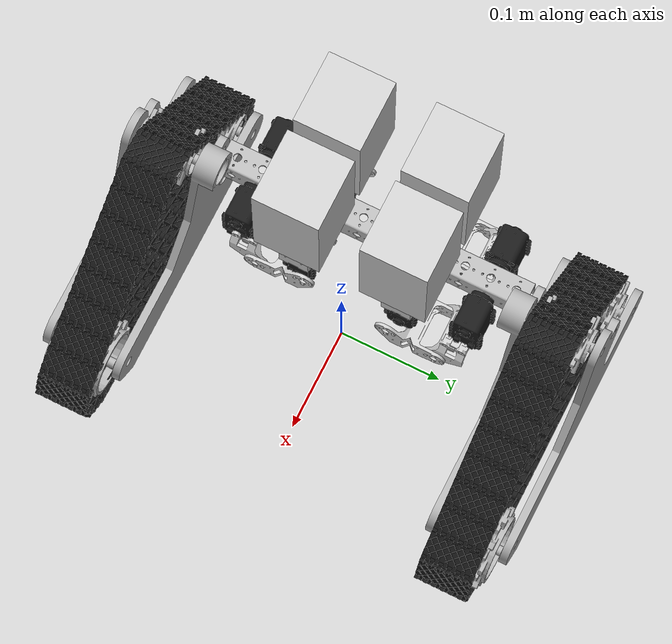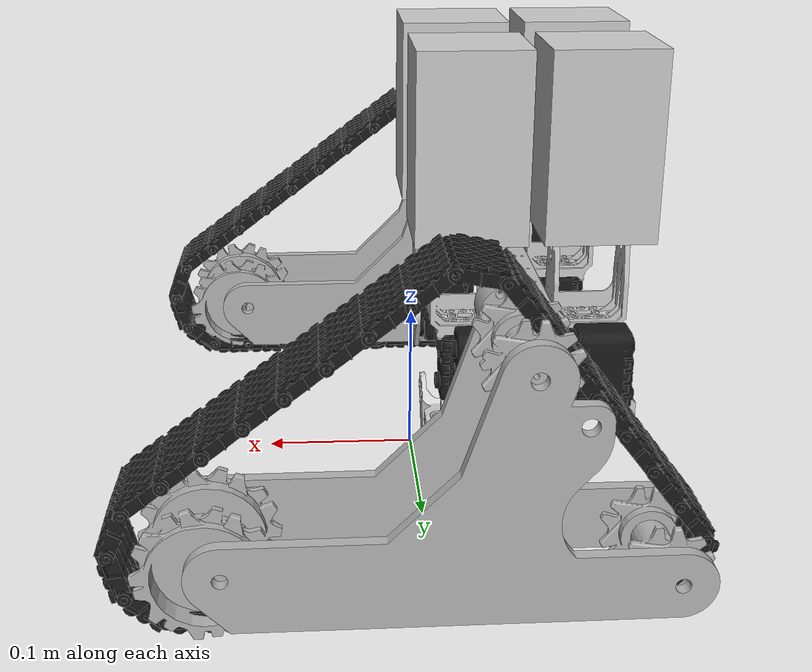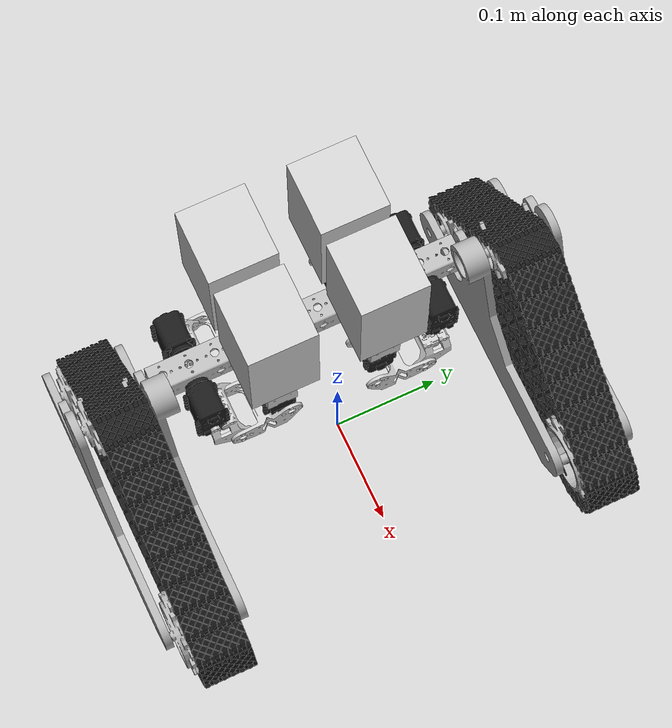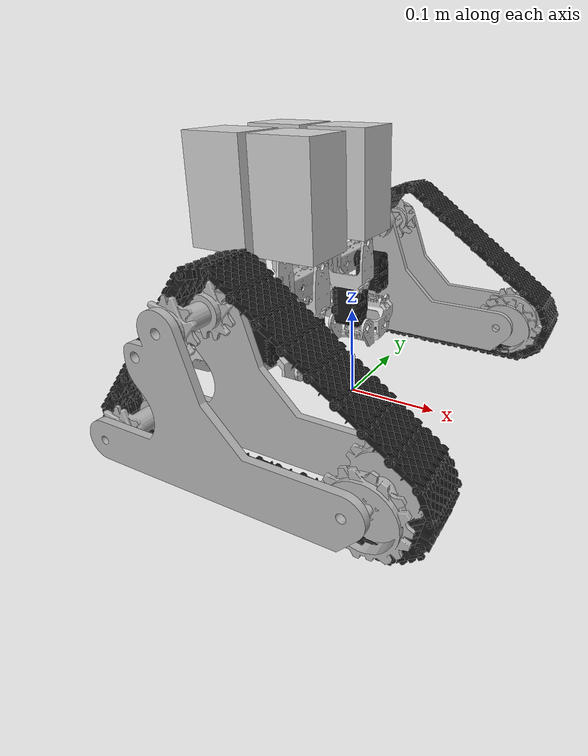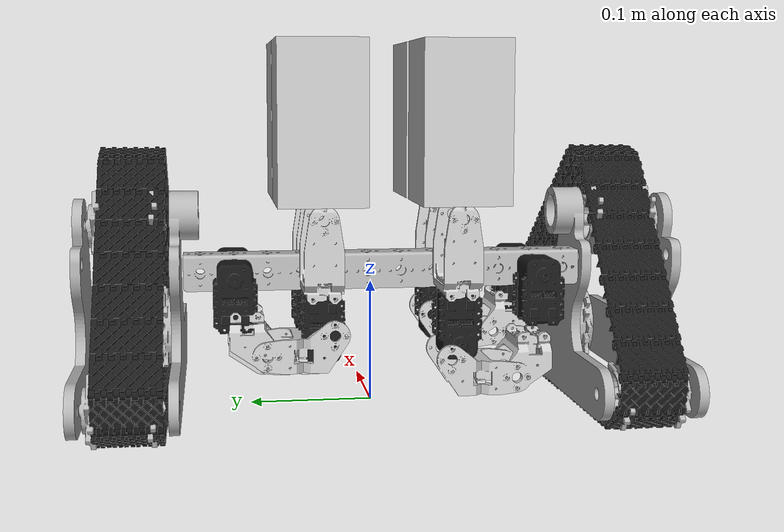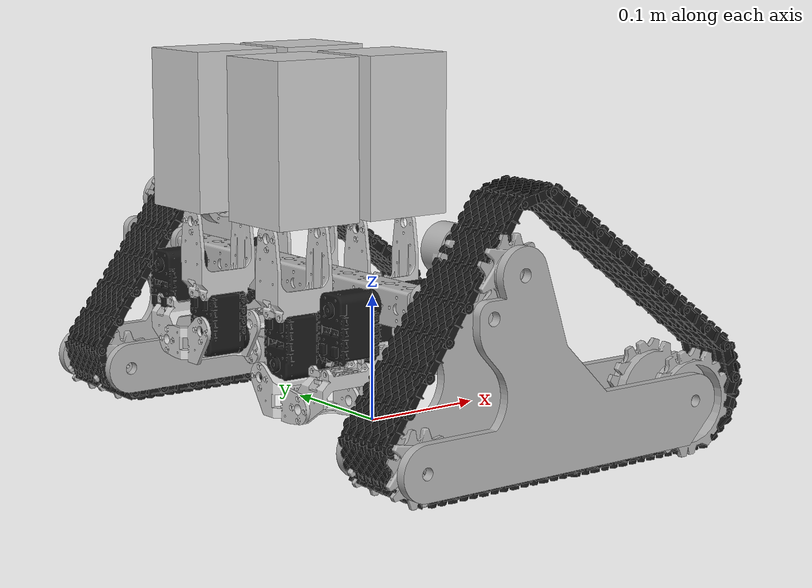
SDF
<sdf version="1.4">
  <model name="aaly">
    <link name="aaly__base_link">
      <self_collide>0</self_collide>
      <pose>-0.07 0 0.1242752 0 0 0</pose>
      <inertial>
        <mass>0.36</mass>
        <inertia>
          <ixx>0.002814604013121458</ixx>
          <ixy>0.0</ixy>
          <ixz>0.0</ixz>
          <iyy>7.17760831593746e-05</iyy>
          <iyz>0.0</iyz>
          <izz>0.0028301708345758957</izz>
        </inertia>
      </inertial>
      <collision name="base_link_collision">
        <geometry>
          <box>
            <size>0.026988 0.3000 0.026988</size>
          </box>
        </geometry>
      </collision>
      <visual name="base_link_visual">
        <geometry>
          <mesh>
            <uri>model://my_tracks/meshes/Horizontal_Support_Bar_ASB-512.dae</uri>
          </mesh>
        </geometry>
      </visual>
    </link>

    <!--Left Back legs-->
    <link name="aaly__knee_left_back_motor">
      <self_collide>1</self_collide>
      <pose>-0.107 0.114400 0.121275 0 0 0</pose>
      <inertial>
        <pose>0 0 -0.012 0 0 0</pose>
        <mass>0.05</mass>
        <inertia>
          <ixx>1.2166047261762851e-05</ixx>
          <ixy>0.0</ixy>
          <ixz>0.0</ixz>
          <iyy>1.4468363602365426e-05</iyy>
          <iyz>0.0</iyz>
          <izz>7.993829324731787e-06</izz>
        </inertia>
      </inertial>
      <collision name="aaly__knee_left_back_motor_collision">
        <geometry>
          <box>
            <size>0.04 0.032 0.050</size>
          </box>
        </geometry>
      </collision>
      <visual name="aaly__knee_left_back_motor_visual">
        <geometry>
          <mesh>
            <uri>model://my_tracks/meshes/AX12-A_origin_same_as_center_of_mass.stl</uri>
          </mesh>
        </geometry>
        <material>
          <ambient>0.2 0.2 0.2 1</ambient>
          <diffuse>0.1 0.1 0.1 1</diffuse>
          <specular>0 0 0 0</specular>
          <emissive>0 0 0 1</emissive>
        </material>
      </visual>
    </link>

    <joint name="aaly__knee_left_back_joint" type="revolute">
      <pose>0 0 0 0 0 0</pose>
      <parent>aaly__base_link</parent>
      <child>aaly__knee_left_back_motor</child>
      <axis>
        <limit>
            <lower>0.0</lower>
            <upper>5.235987755982989</upper>
            <effort>200</effort>
            <velocity>1.0</velocity>
        </limit>
        <xyz>-1 0 0</xyz>
      </axis>
    </joint>

    <link name="aaly__leg_left_back">
      <self_collide>1</self_collide>
      <pose>-0.108500 0.0905 0.065050 0 0 0</pose>
      <inertial>
        <mass>0.04</mass>
        <inertia>
          <ixx>2.69490184257131e-05</ixx>
          <ixy>0.0</ixy>
          <ixz>0.0</ixz>
          <iyy>1.843324918045141e-05</iyy>
          <iyz>0.0</iyz>
          <izz>3.454538603564566e-05</izz>
        </inertia>
      </inertial>
      <collision name="aaly__leg_left_back_collision">
        <geometry>
          <box>
            <size>0.04 0.04 0.025</size>
          </box>
        </geometry>
      </collision>
      <visual name="aaly__leg_left_back_visual">
        <geometry>
          <mesh>
            <uri>model://my_tracks/meshes/Leg_Left_Back.stl</uri>
          </mesh>
        </geometry>
        <material>
          <ambient>0.4 0.4 0.4 1</ambient>
          <diffuse>0.8 0.8 0.8 1</diffuse>
          <specular>0 0 0 0</specular>
          <emissive>0 0 0 1</emissive>
        </material>
      </visual>
    </link>

    <joint name="aaly__leg_left_back_joint" type="fixed">
      <pose>0 0 0 0 0 0</pose>
      <parent>aaly__knee_left_back_motor</parent>
      <child>aaly__leg_left_back</child>
      <axis>
        <xyz>0 0 0</xyz>
      </axis>
    </joint>

    <link name="aaly__thigh_left_back_motor">
      <self_collide>1</self_collide>
      <pose>-0.110000 0.051000 0.071275 3.141592653589793 0 0</pose>
      <inertial>
        <pose>0 0 -0.012 0 0 0</pose>
        <mass>0.05</mass>
        <inertia>
          <ixx>1.2166047261762851e-05</ixx>
          <ixy>0.0</ixy>
          <ixz>0.0</ixz>
          <iyy>1.4468363602365426e-05</iyy>
          <iyz>0.0</iyz>
          <izz>7.993829324731787e-06</izz>
        </inertia>
      </inertial>
      <collision name="aaly__thigh_left_back_motor_collision">
        <geometry>
          <box>
            <size>0.04 0.032 0.050</size>
          </box>
        </geometry>
      </collision>
      <visual name="aaly__thigh_left_back_motor_visual">
        <geometry>
          <mesh>
            <uri>model://my_tracks/meshes/AX12-A_origin_same_as_center_of_mass.stl</uri>
          </mesh>
        </geometry>
        <material>
          <ambient>0.2 0.2 0.2 1</ambient>
          <diffuse>0.1 0.1 0.1 1</diffuse>
          <specular>0 0 0 0</specular>
          <emissive>0 0 0 1</emissive>
        </material>
      </visual>
    </link>

    <joint name="aaly__thigh_left_back_motor_joint" type="revolute">
      <pose>0 0 0 0 0 0</pose>
      <parent>aaly__leg_left_back</parent>
      <child>aaly__thigh_left_back_motor</child>
      <axis>
        <limit>
            <lower>0.0</lower>
            <upper>5.235987755982989</upper>
            <effort>200</effort>
            <velocity>1.0</velocity>
        </limit>
        <xyz>1 0 0</xyz>
      </axis>
    </joint>

    <link name="aaly__thigh_left_back">
      <self_collide>1</self_collide>
      <pose>-0.110000 0.05000 0.127500 0 0 1.57079632679</pose>
      <inertial>
        <mass>0.03</mass>
        <inertia>
          <ixx>2.0103848503359805e-05</ixx>
          <ixy>0.0</ixy>
          <ixz>0.0</ixz>
          <iyy>1.2296884544899207e-05</iyy>
          <iyz>0.0</iyz>
          <izz>1.2205253512522909e-05</izz>
        </inertia>
      </inertial>
      <collision name="aaly__thigh_left_back_collision">
        <geometry>
          <box>
            <size>0.04 0.032 0.030</size>
          </box>
        </geometry>
      </collision>
      <visual name="aaly__thigh_left_back_visual">
        <geometry>
          <mesh>
            <uri>model://my_tracks/meshes/Thigh.dae</uri>
          </mesh>
        </geometry>
        <material>
          <ambient>0.4 0.4 0.4 1</ambient>
          <diffuse>0.8 0.8 0.8 1</diffuse>
          <specular>0 0 0 0</specular>
          <emissive>0 0 0 1</emissive>
        </material>
      </visual>
    </link>

    <joint name="aaly__thigh_left_back_joint" type="fixed">
      <pose>0 0 -0.023 0 0 0</pose>
      <parent>aaly__thigh_left_back_motor</parent>
      <child>aaly__thigh_left_back</child>
      <axis>
        <xyz>0 0 0</xyz>
      </axis>
    </joint>
    <!--Left Back legs-->

    <!--Left Front legs-->
    <link name="aaly__knee_left_front_motor">
      <self_collide>1</self_collide>
      <pose>-0.034 0.114400 0.121275 0 0 3.141592653589793</pose>
      <inertial>
        <pose>0 0 -0.012 0 0 0</pose>
        <mass>0.05</mass>
        <inertia>
          <ixx>1.2166047261762851e-05</ixx>
          <ixy>0.0</ixy>
          <ixz>0.0</ixz>
          <iyy>1.4468363602365426e-05</iyy>
          <iyz>0.0</iyz>
          <izz>7.993829324731787e-06</izz>
        </inertia>
      </inertial>
      <collision name="aaly__knee_left_front_motor_collision">
        <geometry>
          <box>
            <size>0.04 0.032 0.050</size>
          </box>
        </geometry>
      </collision>
      <visual name="aaly__knee_left_front_motor_visual">
        <geometry>
          <mesh>
            <uri>model://my_tracks/meshes/AX12-A_origin_same_as_center_of_mass.stl</uri>
          </mesh>
        </geometry>
        <material>
          <ambient>0.2 0.2 0.2 1</ambient>
          <diffuse>0.1 0.1 0.1 1</diffuse>
          <specular>0 0 0 0</specular>
          <emissive>0 0 0 1</emissive>
        </material>
      </visual>
    </link>

    <joint name="aaly__knee_left_front_joint" type="revolute">
      <pose>0 0 0 0 0 0</pose>
      <parent>aaly__base_link</parent>
      <child>aaly__knee_left_front_motor</child>
      <axis>
        <limit>
            <lower>0.0</lower>
            <upper>5.235987755982989</upper>
            <effort>200</effort>
            <velocity>1.0</velocity>
        </limit>
        <xyz>-1 0 0</xyz>
      </axis>
    </joint>

    <link name="aaly__leg_left_front">
      <self_collide>1</self_collide>
      <pose>-0.03024 0.0905 0.065050 0 0 0</pose>
      <inertial>
        <mass>0.04</mass>
        <inertia>
          <ixx>2.69490184257131e-05</ixx>
          <ixy>0.0</ixy>
          <ixz>0.0</ixz>
          <iyy>1.843324918045141e-05</iyy>
          <iyz>0.0</iyz>
          <izz>3.454538603564566e-05</izz>
        </inertia>
      </inertial>
      <collision name="aaly__leg_left_front_collision">
        <geometry>
          <box>
            <size>0.04 0.04 0.025</size>
          </box>
        </geometry>
      </collision>
      <visual name="aaly__leg_left_front_visual">
        <geometry>
          <mesh>
            <uri>model://my_tracks/meshes/Leg_Left_Front.stl</uri>
          </mesh>
        </geometry>
        <material>
          <ambient>0.4 0.4 0.4 1</ambient>
          <diffuse>0.8 0.8 0.8 1</diffuse>
          <specular>0 0 0 0</specular>
          <emissive>0 0 0 1</emissive>
        </material>
      </visual>
    </link>

    <joint name="aaly__leg_left_front_joint" type="fixed">
      <pose>0 0 0 0 0 0</pose>
      <parent>aaly__knee_left_front_motor</parent>
      <child>aaly__leg_left_front</child>
      <axis>
        <xyz>0 0 0</xyz>
      </axis>
    </joint>

    <link name="aaly__thigh_left_front_motor">
      <self_collide>1</self_collide>
      <pose>-0.031000 0.051000 0.071275 3.141592653589793 0 3.141592653589793</pose>
      <inertial>
        <pose>0 0 -0.012 0 0 0</pose>
        <mass>0.05</mass>
        <inertia>
          <ixx>1.2166047261762851e-05</ixx>
          <ixy>0.0</ixy>
          <ixz>0.0</ixz>
          <iyy>1.4468363602365426e-05</iyy>
          <iyz>0.0</iyz>
          <izz>7.993829324731787e-06</izz>
        </inertia>
      </inertial>
      <collision name="aaly__thigh_left_front_motor_collision">
        <geometry>
          <box>
            <size>0.04 0.032 0.050</size>
          </box>
        </geometry>
      </collision>
      <visual name="aaly__thigh_left_front_motor_visual">
        <geometry>
          <mesh>
            <uri>model://my_tracks/meshes/AX12-A_origin_same_as_center_of_mass.stl</uri>
          </mesh>
        </geometry>
        <material>
          <ambient>0.2 0.2 0.2 1</ambient>
          <diffuse>0.1 0.1 0.1 1</diffuse>
          <specular>0 0 0 0</specular>
          <emissive>0 0 0 1</emissive>
        </material>
      </visual>
    </link>

    <joint name="aaly__thigh_left_front_motor_joint" type="revolute">
      <pose>0 0 0 0 0 0</pose>
      <parent>aaly__leg_left_front</parent>
      <child>aaly__thigh_left_front_motor</child>
      <axis>
        <limit>
            <lower>0.0</lower>
            <upper>5.235987755982989</upper>
            <effort>200</effort>
            <velocity>1.0</velocity>
        </limit>
        <xyz>1 0 0</xyz>
      </axis>
    </joint>

    <link name="aaly__thigh_left_front">
      <self_collide>1</self_collide>
      <pose>-0.031000 0.05000 0.127500 0 0 1.57079632679</pose>
      <inertial>
        <mass>0.03</mass>
        <inertia>
          <ixx>2.0103848503359805e-05</ixx>
          <ixy>0.0</ixy>
          <ixz>0.0</ixz>
          <iyy>1.2296884544899207e-05</iyy>
          <iyz>0.0</iyz>
          <izz>1.2205253512522909e-05</izz>
        </inertia>
      </inertial>
      <collision name="aaly__thigh_left_front_collision">
        <geometry>
          <box>
            <size>0.04 0.032 0.030</size>
          </box>
        </geometry>
      </collision>
      <visual name="aaly__thigh_left_front_visual">
        <geometry>
          <mesh>
            <uri>model://my_tracks/meshes/Thigh.dae</uri>
          </mesh>
        </geometry>
        <material>
          <ambient>0.4 0.4 0.4 1</ambient>
          <diffuse>0.8 0.8 0.8 1</diffuse>
          <specular>0 0 0 0</specular>
          <emissive>0 0 0 1</emissive>
        </material>
      </visual>
    </link>

    <joint name="aaly__thigh_left_joint" type="fixed">
      <pose>0 0 -0.023 0 0 0</pose>
      <parent>aaly__thigh_left_front_motor</parent>
      <child>aaly__thigh_left_front</child>
      <axis>
        <xyz>0 0 0</xyz>
      </axis>
    </joint>
    <!--Left Front legs-->

    <!--Right Back legs-->
    <link name="aaly__knee_right_back_motor">
      <self_collide>1</self_collide>
      <pose>-0.107 -0.114400 0.121275 0 0 0</pose>
      <inertial>
        <pose>0 0 -0.012 0 0 0</pose>
        <mass>0.05</mass>
        <inertia>
          <ixx>1.2166047261762851e-05</ixx>
          <ixy>0.0</ixy>
          <ixz>0.0</ixz>
          <iyy>1.4468363602365426e-05</iyy>
          <iyz>0.0</iyz>
          <izz>7.993829324731787e-06</izz>
        </inertia>
      </inertial>
      <collision name="aaly__knee_right_back_motor_collision">
        <geometry>
          <box>
            <size>0.04 0.032 0.050</size>
          </box>
        </geometry>
      </collision>
      <visual name="aaly__knee_right_back_motor_visual">
        <geometry>
          <mesh>
            <uri>model://my_tracks/meshes/AX12-A_origin_same_as_center_of_mass.stl</uri>
          </mesh>
        </geometry>
        <material>
          <ambient>0.2 0.2 0.2 1</ambient>
          <diffuse>0.1 0.1 0.1 1</diffuse>
          <specular>0 0 0 0</specular>
          <emissive>0 0 0 1</emissive>
        </material>
      </visual>
    </link>

    <joint name="aaly__knee_right_back_joint" type="revolute">
      <pose>0 0 0 0 0 0</pose>
      <parent>aaly__base_link</parent>
      <child>aaly__knee_right_back_motor</child>
      <axis>
        <limit>
            <lower>0.0</lower>
            <upper>5.235987755982989</upper>
            <effort>200</effort>
            <velocity>1.0</velocity>
        </limit>
        <xyz>1 0 0</xyz>
      </axis>
    </joint>

    <link name="aaly__leg_right_back">
      <self_collide>1</self_collide>
      <pose>-0.108500 -0.0905 0.065050 0 0 0</pose>
      <inertial>
        <mass>0.04</mass>
        <inertia>
          <ixx>2.69490184257131e-05</ixx>
          <ixy>0.0</ixy>
          <ixz>0.0</ixz>
          <iyy>1.843324918045141e-05</iyy>
          <iyz>0.0</iyz>
          <izz>3.454538603564566e-05</izz>
        </inertia>
      </inertial>
      <collision name="aaly__leg_right_back_collision">
        <geometry>
          <box>
            <size>0.04 0.04 0.025</size>
          </box>
        </geometry>
      </collision>
      <visual name="aaly__leg_right_back_visual">
        <geometry>
          <mesh>
            <uri>model://my_tracks/meshes/Leg_Right_Back.stl</uri>
          </mesh>
        </geometry>
        <material>
          <ambient>0.4 0.4 0.4 1</ambient>
          <diffuse>0.8 0.8 0.8 1</diffuse>
          <specular>0 0 0 0</specular>
          <emissive>0 0 0 1</emissive>
        </material>
      </visual>
    </link>

    <joint name="aaly__leg_right_back_joint" type="fixed">
      <pose>0 0 0 0 0 0</pose>
      <parent>aaly__knee_right_back_motor</parent>
      <child>aaly__leg_right_back</child>
      <axis>
        <xyz>0 0 0</xyz>
      </axis>
    </joint>

    <link name="aaly__thigh_right_back_motor">
      <self_collide>1</self_collide>
      <pose>-0.110000 -0.051000 0.071275 3.141592653589793 0 0</pose>
      <inertial>
        <pose>0 0 -0.012 0 0 0</pose>
        <mass>0.05</mass>
        <inertia>
          <ixx>1.2166047261762851e-05</ixx>
          <ixy>0.0</ixy>
          <ixz>0.0</ixz>
          <iyy>1.4468363602365426e-05</iyy>
          <iyz>0.0</iyz>
          <izz>7.993829324731787e-06</izz>
        </inertia>
      </inertial>
      <collision name="aaly__thigh_right_back_motor_collision">
        <geometry>
          <box>
            <size>0.04 0.032 0.050</size>
          </box>
        </geometry>
      </collision>
      <visual name="aaly__thigh_right_back_motor_visual">
        <geometry>
          <mesh>
            <uri>model://my_tracks/meshes/AX12-A_origin_same_as_center_of_mass.stl</uri>
          </mesh>
        </geometry>
        <material>
          <ambient>0.2 0.2 0.2 1</ambient>
          <diffuse>0.1 0.1 0.1 1</diffuse>
          <specular>0 0 0 0</specular>
          <emissive>0 0 0 1</emissive>
        </material>
      </visual>
    </link>

    <joint name="aaly__thigh_right_back_motor_joint" type="revolute">
      <pose>0 0 0 0 0 0</pose>
      <parent>aaly__leg_right_back</parent>
      <child>aaly__thigh_right_back_motor</child>
      <axis>
        <limit>
            <lower>0.0</lower>
            <upper>5.235987755982989</upper>
            <effort>200</effort>
            <velocity>1.0</velocity>
        </limit>
        <xyz>-1 0 0</xyz>
      </axis>
    </joint>

    <link name="aaly__thigh_right_back">
      <self_collide>1</self_collide>
      <pose>-0.110000 -0.05200 0.127500 0 0 1.57079632679</pose>
      <inertial>
        <mass>0.03</mass>
        <inertia>
          <ixx>2.0103848503359805e-05</ixx>
          <ixy>0.0</ixy>
          <ixz>0.0</ixz>
          <iyy>1.2296884544899207e-05</iyy>
          <iyz>0.0</iyz>
          <izz>1.2205253512522909e-05</izz>
        </inertia>
      </inertial>
      <collision name="aaly__thigh_right_back_collision">
        <geometry>
          <box>
            <size>0.04 0.032 0.030</size>
          </box>
        </geometry>
      </collision>
      <visual name="aaly__thigh_right_back_visual">
        <geometry>
          <mesh>
            <uri>model://my_tracks/meshes/Thigh.dae</uri>
          </mesh>
        </geometry>
        <material>
          <ambient>0.4 0.4 0.4 1</ambient>
          <diffuse>0.8 0.8 0.8 1</diffuse>
          <specular>0 0 0 0</specular>
          <emissive>0 0 0 1</emissive>
        </material>
      </visual>
    </link>

    <joint name="aaly__thigh_right_back_joint" type="fixed">
      <pose>0 0 0 -0.023 0 0</pose>
      <parent>aaly__thigh_right_back_motor</parent>
      <child>aaly__thigh_right_back</child>
      <axis>
        <xyz>0 0 0</xyz>
      </axis>
    </joint>
    <!--Right Back legs-->

    <!--Right Front legs-->
    <link name="aaly__knee_right_front_motor">
      <self_collide>1</self_collide>
      <pose>-0.034 -0.114400 0.121275 0 0 3.141592653589793</pose>
      <inertial>
        <pose>0 0 -0.012 0 0 0</pose>
        <mass>0.05</mass>
        <inertia>
          <ixx>1.2166047261762851e-05</ixx>
          <ixy>0.0</ixy>
          <ixz>0.0</ixz>
          <iyy>1.4468363602365426e-05</iyy>
          <iyz>0.0</iyz>
          <izz>7.993829324731787e-06</izz>
        </inertia>
      </inertial>
      <collision name="aaly__knee_right_front_motor_collision">
        <geometry>
          <box>
            <size>0.04 0.032 0.050</size>
          </box>
        </geometry>
      </collision>
      <visual name="aaly__knee_right_front_motor_visual">
        <geometry>
          <mesh>
            <uri>model://my_tracks/meshes/AX12-A_origin_same_as_center_of_mass.stl</uri>
          </mesh>
        </geometry>
        <material>
          <ambient>0.2 0.2 0.2 1</ambient>
          <diffuse>0.1 0.1 0.1 1</diffuse>
          <specular>0 0 0 0</specular>
          <emissive>0 0 0 1</emissive>
        </material>
      </visual>
    </link>

    <joint name="aaly__knee_right_front_joint" type="revolute">
      <pose>0 0 0 0 0 0</pose>
      <parent>aaly__base_link</parent>
      <child>aaly__knee_right_front_motor</child>
      <axis>
        <limit>
            <lower>0.0</lower>
            <upper>5.235987755982989</upper>
            <effort>200</effort>
            <velocity>1.0</velocity>
        </limit>
        <xyz>1 0 0</xyz>
      </axis>
    </joint>

    <link name="aaly__leg_right_front">
      <self_collide>1</self_collide>
      <pose>-0.03024 -0.0905 0.065050 0 0 0</pose>
      <inertial>
        <mass>0.04</mass>
        <inertia>
          <ixx>2.69490184257131e-05</ixx>
          <ixy>0.0</ixy>
          <ixz>0.0</ixz>
          <iyy>1.843324918045141e-05</iyy>
          <iyz>0.0</iyz>
          <izz>3.454538603564566e-05</izz>
        </inertia>
      </inertial>
      <collision name="aaly__leg_right_front_collision">
        <geometry>
          <box>
            <size>0.04 0.04 0.025</size>
          </box>
        </geometry>
      </collision>
      <visual name="aaly__leg_right_front_visual">
        <geometry>
          <mesh>
            <uri>model://my_tracks/meshes/Leg_Right_Front.stl</uri>
          </mesh>
        </geometry>
        <material>
          <ambient>0.4 0.4 0.4 1</ambient>
          <diffuse>0.8 0.8 0.8 1</diffuse>
          <specular>0 0 0 0</specular>
          <emissive>0 0 0 1</emissive>
        </material>
      </visual>
    </link>

    <joint name="aaly__leg_right_front_joint" type="fixed">
      <pose>0 0 0 0 0 0</pose>
      <parent>aaly__knee_right_front_motor</parent>
      <child>aaly__leg_right_front</child>
      <axis>
        <xyz>0 0 0</xyz>
      </axis>
    </joint>

    <link name="aaly__thigh_right_front_motor">
      <self_collide>1</self_collide>
      <pose>-0.02974 -0.051000 0.071275 3.141592653589793 0 0</pose>
      <inertial>
        <pose>0 0 -0.012 0 0 0</pose>
        <mass>0.05</mass>
        <inertia>
          <ixx>1.2166047261762851e-05</ixx>
          <ixy>0.0</ixy>
          <ixz>0.0</ixz>
          <iyy>1.4468363602365426e-05</iyy>
          <iyz>0.0</iyz>
          <izz>7.993829324731787e-06</izz>
        </inertia>
      </inertial>
      <collision name="aaly__thigh_right_front_motor_collision">
        <geometry>
          <box>
            <size>0.04 0.032 0.050</size>
          </box>
        </geometry>
      </collision>
      <visual name="aaly__thigh_right_front_motor_visual">
        <geometry>
          <mesh>
            <uri>model://my_tracks/meshes/AX12-A_origin_same_as_center_of_mass.stl</uri>
          </mesh>
        </geometry>
        <material>
          <ambient>0.2 0.2 0.2 1</ambient>
          <diffuse>0.1 0.1 0.1 1</diffuse>
          <specular>0 0 0 0</specular>
          <emissive>0 0 0 1</emissive>
        </material>
      </visual>
    </link>

    <joint name="aaly__thigh_right_front_motor_joint" type="revolute">
      <pose>0 0 0 0 0 0</pose>
      <parent>aaly__leg_right_front</parent>
      <child>aaly__thigh_right_front_motor</child>
      <axis>
        <limit>
            <lower>0.0</lower>
            <upper>5.235987755982989</upper>
            <effort>200</effort>
            <velocity>1.0</velocity>
        </limit>
        <xyz>-1 0 0</xyz>
      </axis>
    </joint>

    <link name="aaly__thigh_right_front">
      <self_collide>1</self_collide>
      <pose>-0.030000 -0.05200 0.127500 0 0 1.57079632679</pose>
      <inertial>
        <mass>0.03</mass>
        <inertia>
          <ixx>2.0103848503359805e-05</ixx>
          <ixy>0.0</ixy>
          <ixz>0.0</ixz>
          <iyy>1.2296884544899207e-05</iyy>
          <iyz>0.0</iyz>
          <izz>1.2205253512522909e-05</izz>
        </inertia>
      </inertial>
      <collision name="aaly__thigh_right_front_collision">
        <geometry>
          <box>
            <size>0.04 0.032 0.030</size>
          </box>
        </geometry>
      </collision>
      <visual name="aaly__thigh_right_front_visual">
        <geometry>
          <mesh>
            <uri>model://my_tracks/meshes/Thigh.dae</uri>
          </mesh>
        </geometry>
        <material>
          <ambient>0.4 0.4 0.4 1</ambient>
          <diffuse>0.8 0.8 0.8 1</diffuse>
          <specular>0 0 0 0</specular>
          <emissive>0 0 0 1</emissive>
        </material>
      </visual>
    </link>

    <joint name="aaly__thigh_right_joint" type="fixed">
      <pose>0 0 -0.023 0 0 0</pose>
      <parent>aaly__thigh_right_front_motor</parent>
      <child>aaly__thigh_right_front</child>
      <axis>
        <xyz>0 0 0</xyz>
      </axis>
    </joint>
    <!--Right Front legs-->

    <!-- Body -->

    <link name="aaly__body1">
      <self_collide>1</self_collide>
      <pose>-0.030000 -0.05200 0.235000 0 0 0</pose>
      <inertial>
        <mass>0.05</mass>
        <inertia>
          <ixx>7.760416666666666e-05</ixx>
          <ixy>0.0</ixy>
          <ixz>0.0</ixz>
          <iyy>8.041666666666667e-05</iyy>
          <iyz>0.0</iyz>
          <izz>3.802083333333334e-05</izz>
        </inertia>
      </inertial>
      <collision name="aaly__body1_collision">
        <geometry>
          <box>
            <size>0.07 0.065 0.12</size>
          </box>
        </geometry>
      </collision>
      <visual name="aaly__body1_visual">
        <geometry>
          <box>
            <size>0.07 0.065 0.12</size>
          </box>
        </geometry>
        <material>
          <ambient>0.4 0.4 0.4 1</ambient>
          <diffuse>0.8 0.8 0.8 1</diffuse>
          <specular>0 0 0 0</specular>
          <emissive>0 0 0 1</emissive>
        </material>
      </visual>
    </link>

    <link name="aaly__body2">
      <self_collide>1</self_collide>
      <pose>-0.110000 -0.05200 0.235000 0 0 0</pose>
      <inertial>
        <mass>0.05</mass>
        <inertia>
          <ixx>7.760416666666666e-05</ixx>
          <ixy>0.0</ixy>
          <ixz>0.0</ixz>
          <iyy>8.041666666666667e-05</iyy>
          <iyz>0.0</iyz>
          <izz>3.802083333333334e-05</izz>
        </inertia>
      </inertial>
      <collision name="aaly__body2_collision">
        <geometry>
          <box>
            <size>0.07 0.065 0.12</size>
          </box>
        </geometry>
      </collision>
      <visual name="aaly__body2_visual">
        <geometry>
          <box>
            <size>0.07 0.065 0.12</size>
          </box>
        </geometry>
        <material>
          <ambient>0.4 0.4 0.4 1</ambient>
          <diffuse>0.8 0.8 0.8 1</diffuse>
          <specular>0 0 0 0</specular>
          <emissive>0 0 0 1</emissive>
        </material>
      </visual>
    </link>

    <link name="aaly__body3">
      <self_collide>1</self_collide>
      <pose>-0.030000 0.05200 0.235000 0 0 0</pose>
      <inertial>
        <mass>0.05</mass>
        <inertia>
          <ixx>7.760416666666666e-05</ixx>
          <ixy>0.0</ixy>
          <ixz>0.0</ixz>
          <iyy>8.041666666666667e-05</iyy>
          <iyz>0.0</iyz>
          <izz>3.802083333333334e-05</izz>
        </inertia>
      </inertial>
      <collision name="aaly__body1_collision">
        <geometry>
          <box>
            <size>0.07 0.065 0.12</size>
          </box>
        </geometry>
      </collision>
      <visual name="aaly__body1_visual">
        <geometry>
          <box>
            <size>0.07 0.065 0.12</size>
          </box>
        </geometry>
        <material>
          <ambient>0.4 0.4 0.4 1</ambient>
          <diffuse>0.8 0.8 0.8 1</diffuse>
          <specular>0 0 0 0</specular>
          <emissive>0 0 0 1</emissive>
        </material>
      </visual>
    </link>

    <link name="aaly__body4">
      <self_collide>1</self_collide>
      <pose>-0.110000 0.05200 0.235000 0 0 0</pose>
      <inertial>
        <mass>0.05</mass>
        <inertia>
          <ixx>7.760416666666666e-05</ixx>
          <ixy>0.0</ixy>
          <ixz>0.0</ixz>
          <iyy>8.041666666666667e-05</iyy>
          <iyz>0.0</iyz>
          <izz>3.802083333333334e-05</izz>
        </inertia>
      </inertial>
      <collision name="aaly__body2_collision">
        <geometry>
          <box>
            <size>0.07 0.065 0.12</size>
          </box>
        </geometry>
      </collision>
      <visual name="aaly__body2_visual">
        <geometry>
          <box>
            <size>0.07 0.065 0.12</size>
          </box>
        </geometry>
        <material>
          <ambient>0.4 0.4 0.4 1</ambient>
          <diffuse>0.8 0.8 0.8 1</diffuse>
          <specular>0 0 0 0</specular>
          <emissive>0 0 0 1</emissive>
        </material>
      </visual>
    </link>

    <joint name="aaly__body_front_right_joint" type="revolute">
      <pose>0 0 -0.065 0 0 0</pose>
      <parent>aaly__thigh_right_front</parent>
      <child>aaly__body1</child>
      <axis>
        <limit>
            <lower>-5.235987755982989</lower>
            <upper>5.235987755982989</upper>
            <effort>200</effort>
            <velocity>1.0</velocity>
        </limit>
        <xyz>1 0 0</xyz>
      </axis>
    </joint>

    <joint name="aaly__body_back_right_joint" type="revolute">
      <pose>0 0 -0.065 0 0 0</pose>
      <parent>aaly__thigh_right_back</parent>
      <child>aaly__body2</child>
      <axis>
        <limit>
            <lower>-5.235987755982989</lower>
            <upper>5.235987755982989</upper>
            <effort>200</effort>
            <velocity>1.0</velocity>
        </limit>
        <xyz>1 0 0</xyz>
      </axis>
    </joint>

    <joint name="aaly__body_front_left_joint" type="revolute">
      <pose>0 0 -0.065 0 0 0</pose>
      <parent>aaly__thigh_left_front</parent>
      <child>aaly__body3</child>
      <axis>
        <limit>
            <lower>-5.235987755982989</lower>
            <upper>5.235987755982989</upper>
            <effort>200</effort>
            <velocity>1.0</velocity>
        </limit>
        <xyz>1 0 0</xyz>
      </axis>
    </joint>

    <joint name="aaly__body_back_left_joint" type="revolute">
      <pose>0 0 -0.065 0 0 0</pose>
      <parent>aaly__thigh_left_back</parent>
      <child>aaly__body4</child>
      <axis>
        <limit>
            <lower>-5.235987755982989</lower>
            <upper>5.235987755982989</upper>
            <effort>200</effort>
            <velocity>1.0</velocity>
        </limit>
        <xyz>1 0 0</xyz>
      </axis>
    </joint>

    <joint name="aaly__body12_joint" type="fixed">
      <pose>0.040 0 0.00 0 0 0</pose>
      <parent>aaly__body1</parent>
      <child>aaly__body2</child>
      <axis>
        <xyz>0 0 0</xyz>
      </axis>
    </joint>

    <joint name="aaly__body34_joint" type="fixed">
      <pose>0.040 0 0.00 0 0 0</pose>
      <parent>aaly__body3</parent>
      <child>aaly__body4</child>
      <axis>
        <xyz>0 0 0</xyz>
      </axis>
    </joint>
    <!-- BODY END -->

    <link name="aaly__Right_Side_Track_Support">
      <self_collide>1</self_collide>
      <pose>-0.0137385 -0.15812 0.070625 0 0 0</pose>
      <inertial>
        <mass>0.15</mass>
        <inertia>
          <ixx>0.00010520383183873306</ixx>
          <ixy>-9.148702320585518e-07</ixy>
          <ixz>3.7647066170409417e-05</ixz>
          <iyy>0.00032229348287662684</iyy>
          <iyz>2.722753728174257e-06</iyz>
          <izz>0.0002182293357979667</izz>
        </inertia>
      </inertial>
      <collision name="Right_Side_Track_Support_collision">
        <pose>0 0 0.015 0 0 0</pose>
        <geometry>
          <mesh>
            <uri>model://my_tracks/meshes/Track_Support_Collision_Mesh.dae</uri>
          </mesh>
        </geometry>
        <surface>
          <friction>
            <ode><mu>0.0</mu><mu2>0.0</mu2></ode>
          </friction>
        </surface>
      </collision>
      <visual name="Right_Side_Track_Support_visual">
        <geometry>
          <mesh>
            <uri>model://my_tracks/meshes/Track_Support_Left_Side.dae</uri>
          </mesh>
        </geometry>
      </visual>
    </link>
    <joint name="aaly__Right_Track_Side_joint" type="fixed">
      <pose>-0.05749 0.004 0.05773 0 0 0</pose>
      <parent>aaly__base_link</parent>
      <child>aaly__Right_Side_Track_Support</child>
      <axis>
        <xyz>0 0 0</xyz>
      </axis>
    </joint>

    <link name="aaly__Left_Side_Track_Support">
      <self_collide>1</self_collide>
      <pose>-0.0137385 0.15812 0.070625 0 0 0</pose>
      <inertial>
        <mass>0.15</mass>
        <inertia>
          <ixx>0.00010520383183873306</ixx>
          <ixy>-9.148702320585518e-07</ixy>
          <ixz>3.7647066170409417e-05</ixz>
          <iyy>0.00032229348287662684</iyy>
          <iyz>2.722753728174257e-06</iyz>
          <izz>0.0002182293357979667</izz>
        </inertia>
      </inertial>
      <collision name="Left_Side_Track_Support_collision">
        <pose>0 0 0.015 0 0 0</pose>
        <geometry>
          <mesh>
            <uri>model://my_tracks/meshes/Track_Support_Collision_Mesh.dae</uri>
          </mesh>
        </geometry>
        <surface>
          <friction>
            <ode><mu>0.0</mu><mu2>0.0</mu2></ode>
          </friction>
        </surface>
      </collision>
      <visual name="Left_Side_Track_Support_visual">
        <geometry>
          <mesh>
            <uri>model://my_tracks/meshes/Track_Support_Right_Side.dae</uri>
          </mesh>
        </geometry>
      </visual>
    </link>
    <joint name="aaly__Left_Track_Side_joint" type="fixed">
      <pose>-0.05749 -0.004 0.05773 0 0 0</pose>
      <parent>aaly__base_link</parent>
      <child>aaly__Left_Side_Track_Support</child>
      <axis>
        <xyz>0 0 0</xyz>
      </axis>
    </joint>

    <link name="aaly__drum1">
      <self_collide>1</self_collide>
      <pose>-0.1248385 -0.19612 0.030 1.57079632679 0 0</pose>
      <inertial>
        <mass>0.1</mass>
        <inertia>
          <ixx>2.787405275215884e-05</ixx>
          <ixy>0.0</ixy>
          <ixz>0.0</ixz>
          <iyy>2.7903424778241207e-05</iyy>
          <iyz>0.0</iyz>
          <izz>1.7975679962403806e-05</izz>
        </inertia>
      </inertial>
      <collision name="drum1_collision">
        <geometry>
          <cylinder>
            <radius>0.026925</radius>
            <length>0.05124</length>
          </cylinder>
        </geometry>
        <surface>
          <friction>
            <ode><mu>100000.0</mu><mu2>100000.0</mu2></ode>
          </friction>
        </surface>
    </collision>
      <visual name="drum1_visual">
        <geometry>
          <mesh>
            <uri>model://my_tracks/meshes/Lynx_Sproket6in_Hub13.dae</uri>
          </mesh>
        </geometry>
      </visual>
    </link>
    <joint name="aaly__drum_joint1" type="revolute">
      <pose>0 0 0 0 0 0</pose>
      <parent>aaly__Right_Side_Track_Support</parent>
      <child>aaly__drum1</child>
      <axis>
        <xyz>0 1 0</xyz>
      </axis>
    </joint>

    <link name="aaly__drum2">
      <self_collide>1</self_collide>
      <pose>-0.1248385 0.19612 0.030 1.57079632679 0 0</pose>
      <inertial>
        <mass>0.1</mass>
        <inertia>
          <ixx>2.787405275215884e-05</ixx>
          <ixy>0.0</ixy>
          <ixz>0.0</ixz>
          <iyy>2.7903424778241207e-05</iyy>
          <iyz>0.0</iyz>
          <izz>1.7975679962403806e-05</izz>
        </inertia>
      </inertial>
      <collision name="drum2_collision">
        <geometry>
          <cylinder>
            <radius>0.026925</radius>
            <length>0.05124</length>
          </cylinder>
        </geometry>
        <surface>
          <friction>
            <ode><mu>100000.0</mu><mu2>100000.0</mu2></ode>
          </friction>
        </surface>
      </collision>
      <visual name="drum2_visual">
        <geometry>
          <mesh>
            <uri>model://my_tracks/meshes/Lynx_Sproket6in_Hub13.dae</uri>
          </mesh>
        </geometry>
      </visual>
    </link>
    <joint name="aaly__drum_joint2" type="revolute">
      <pose>0 0 0 0 0 0</pose>
      <parent>aaly__Left_Side_Track_Support</parent>
      <child>aaly__drum2</child>
      <axis>
        <xyz>0 1 0</xyz>
      </axis>
    </joint>
    <link name="aaly__drum3">
      <self_collide>1</self_collide>
      <pose>0.1288385 -0.19612 0.037625 1.57079632679 0 0</pose>
      <inertial>
        <mass>0.2</mass>
        <inertia>
          <ixx>0.00010790475895594018</ixx>
          <ixy>0.0</ixy>
          <ixz>0.0</ixz>
          <iyy>0.00010774994581540083</iyy>
          <iyz>0.0</iyz>
          <izz>0.00012753506517633218</izz>
        </inertia>
      </inertial>
      <collision name="drum3_collision">
        <geometry>
          <cylinder>
            <radius>0.036625</radius>
            <length>0.05124</length>
          </cylinder>
        </geometry>
        <surface>
          <friction>
            <ode><mu>100000.0</mu><mu2>100000.0</mu2></ode>
          </friction>
        </surface>
      </collision>
      <visual name="drum3_visual">
        <geometry>
          <mesh>
            <uri>model://my_tracks/meshes/Lynx_Sproket9in_Hub13.dae</uri>
          </mesh>
        </geometry>
      </visual>
    </link>
    <joint name="aaly__drum_joint3" type="revolute">
      <pose>0 0 0 0 0 0</pose>
      <parent>aaly__Right_Side_Track_Support</parent>
      <child>aaly__drum3</child>
      <axis>
        <xyz>0 1 0</xyz>
      </axis>
    </joint>
    <link name="aaly__drum4">
      <self_collide>1</self_collide>
      <pose>0.1288385 0.19612 0.037625 1.57079632679 0 0</pose>
      <inertial>
        <mass>0.2</mass>
        <inertia>
          <ixx>0.00010790475895594018</ixx>
          <ixy>0.0</ixy>
          <ixz>0.0</ixz>
          <iyy>0.00010774994581540083</iyy>
          <iyz>0.0</iyz>
          <izz>0.00012753506517633218</izz>
        </inertia>
      </inertial>
      <collision name="drum4_collision">
        <geometry>
          <cylinder>
            <radius>0.036625</radius>
            <length>0.05124</length>
          </cylinder>
        </geometry>
        <surface>
          <friction>
            <ode><mu>100000.0</mu><mu2>100000.0</mu2></ode>
          </friction>
        </surface>
      </collision>
      <visual name="drum4_visual">
        <geometry>
          <mesh>
            <uri>model://my_tracks/meshes/Lynx_Sproket9in_Hub13.dae</uri>
          </mesh>
        </geometry>
      </visual>
    </link>
    <joint name="aaly__drum_joint4" type="revolute">
      <pose>0 0 0 0 0 0</pose>
      <parent>aaly__Left_Side_Track_Support</parent>
      <child>aaly__drum4</child>
      <axis>
        <xyz>0 1 0</xyz>
      </axis>
    </joint>
    <link name="aaly__drum5">
      <self_collide>1</self_collide>
      <pose>-0.0460507 -0.19612 0.154342 1.57079632679 0 0</pose>
      <inertial>
        <mass>0.1</mass>
        <inertia>
          <ixx>2.787405275215884e-05</ixx>
          <ixy>0.0</ixy>
          <ixz>0.0</ixz>
          <iyy>2.7903424778241207e-05</iyy>
          <iyz>0.0</iyz>
          <izz>1.7975679962403806e-05</izz>
        </inertia>
      </inertial>
      <collision name="drum5_collision">
        <geometry>
          <cylinder>
            <radius>0.027025</radius>
            <length>0.05124</length>
          </cylinder>
        </geometry>
        <surface>
          <friction>
            <ode><mu>100000.0</mu><mu2>100000.0</mu2></ode>
          </friction>
        </surface>
      </collision>
      <visual name="drum5_visual">
        <geometry>
          <mesh>
            <uri>model://my_tracks/meshes/Lynx_Sproket6in_Hub13.dae</uri>
          </mesh>
        </geometry>
      </visual>
    </link>
    <joint name="aaly__drum_joint5" type="revolute">
      <pose>0 0 0 0 0 0</pose>
      <parent>aaly__Right_Side_Track_Support</parent>
      <child>aaly__drum5</child>
      <axis>
        <xyz>0 1 0</xyz>
      </axis>
    </joint>

    <link name="aaly__drum6">
      <self_collide>1</self_collide>
      <pose>-0.0460507 0.19612 0.154342 1.57079632679 0 0</pose>
      <inertial>
        <mass>0.1</mass>
        <inertia>
          <ixx>2.787405275215884e-05</ixx>
          <ixy>0.0</ixy>
          <ixz>0.0</ixz>
          <iyy>2.7903424778241207e-05</iyy>
          <iyz>0.0</iyz>
          <izz>1.7975679962403806e-05</izz>
        </inertia>
      </inertial>
      <collision name="drum6_collision">
        <geometry>
          <cylinder>
            <radius>0.027025</radius>
            <length>0.05124</length>
          </cylinder>
        </geometry>
        <surface>
          <friction>
            <ode><mu>100000.0</mu><mu2>100000.0</mu2></ode>
          </friction>
        </surface>
      </collision>
      <visual name="drum6_visual">
        <geometry>
          <mesh>
            <uri>model://my_tracks/meshes/Lynx_Sproket6in_Hub13.dae</uri>
          </mesh>
        </geometry>
      </visual>
    </link>
    <joint name="aaly__drum_joint6" type="revolute">
      <pose>0 0 0 0 0 0</pose>
      <parent>aaly__Left_Side_Track_Support</parent>
      <child>aaly__drum6</child>
      <axis>
        <xyz>0 1 0</xyz>
      </axis>
    </joint>

    <link name="aaly__Right_Side_Track_Cover">
      <self_collide>1</self_collide>
      <pose>-0.0134385 -0.23112 0.061625 0 0 0</pose>
      <inertial>
        <mass>0.15</mass>
        <inertia>
          <ixx>0.00010520383183873306</ixx>
          <ixy>-9.148702320585518e-07</ixy>
          <ixz>3.7647066170409417e-05</ixz>
          <iyy>0.00032229348287662684</iyy>
          <iyz>2.722753728174257e-06</iyz>
          <izz>0.0002182293357979667</izz>
        </inertia>
      </inertial>
      <collision name="Right_Side_Track_Cover_collision">
        <pose>0 0 0.015 0 0 0</pose>
        <geometry>
          <mesh>
            <uri>model://my_tracks/meshes/Track_Support_Collision_Mesh.dae</uri>
          </mesh>
        </geometry>
        <surface>
          <friction>
            <ode><mu>0.0</mu><mu2>0.0</mu2></ode>
          </friction>
        </surface>
      </collision>
      <visual name="Right_Side_Track_Cover_visual">
        <geometry>
          <mesh>
            <uri>model://my_tracks/meshes/Track_Support_Cover_Side.dae</uri>
          </mesh>
        </geometry>
      </visual>
    </link>
    <joint name="aaly__Right_Side_Track_Cover_joint" type="fixed">
      <pose>0 0 0 0 0 0</pose>
      <parent>aaly__Right_Side_Track_Support</parent>
      <child>aaly__Right_Side_Track_Cover</child>
      <axis>
        <xyz>0 0 0</xyz>
      </axis>
    </joint>

    <link name="aaly__Left_Side_Track_Cover">
      <self_collide>1</self_collide>
      <pose>-0.0134385 0.23112 0.061625 0 0 0</pose>
      <inertial>
        <mass>0.15</mass>
        <inertia>
          <ixx>0.00010520383183873306</ixx>
          <ixy>-9.148702320585518e-07</ixy>
          <ixz>3.7647066170409417e-05</ixz>
          <iyy>0.00032229348287662684</iyy>
          <iyz>2.722753728174257e-06</iyz>
          <izz>0.0002182293357979667</izz>
        </inertia>
      </inertial>
      <collision name="Left_Side_Track_Cover_collision">
        <pose>0 0 0.015 0 0 0</pose>
        <geometry>
          <mesh>
            <uri>model://my_tracks/meshes/Track_Support_Collision_Mesh.dae</uri>
          </mesh>
        </geometry>
        <surface>
          <friction>
            <ode><mu>0.0</mu><mu2>0.0</mu2></ode>
          </friction>
        </surface>
      </collision>
      <visual name="Left_Side_Track_Cover_visual">
        <geometry>
          <mesh>
            <uri>model://my_tracks/meshes/Track_Support_Cover_Side.dae</uri>
          </mesh>
        </geometry>
      </visual>
    </link>
    <joint name="aaly__Left_Side_Track_Cover_joint" type="fixed">
      <pose>0 0 0 0 0 0</pose>
      <parent>aaly__Left_Side_Track_Support</parent>
      <child>aaly__Left_Side_Track_Cover</child>
      <axis>
        <xyz>0 0 0</xyz>
      </axis>
    </joint>

  <!-- Track Pads -->

    <link name="right_pad1">
      <self_collide>1</self_collide>
      <pose>0.0276163221427 0.191842 0.0055 0 0.0 0</pose>
      <inertial>
        <mass>0.035</mass>
        <inertia>
          <ixx>8.251900108577635e-06</ixx>
          <ixy>0.0</ixy>
          <ixz>0.0</ixz>
          <iyy>3.3659066232356143e-06</iyy>
          <iyz>0.0</iyz>
          <izz>1.1020629750271444e-05</izz>
        </inertia>
      </inertial>
      <collision name="right_pad1_collision">
        <geometry>
          <box>
            <size>0.0275 0.054 0.011</size>
          </box>
        </geometry>
      </collision>
      <visual name="right_pad1_visual">
        <geometry>
          <mesh>
            <uri>model://my_tracks/meshes/Lynx_Track_2in.dae</uri>
          </mesh>
        </geometry>
        <material>
          <ambient>0.2 0.2 0.2 1</ambient>
          <diffuse>0.1 0.1 0.1 1</diffuse>
          <specular>0 0 0 0</specular>
          <emissive>0 0 0 1</emissive>
        </material>
      </visual>
    </link>
    <joint name="right_pad_joint1" type="revolute">
      <pose>-0.0138081610714 0 0 0 0 0</pose>
      <parent>right_pad1</parent>
      <child>right_pad2</child>
      <axis>
        <xyz>0 1 0</xyz>
      </axis>
    </joint>
    <link name="right_pad2">
      <self_collide>1</self_collide>
      <pose>0.0552326442854 0.191842 0.0055 0 0.0 0</pose>
      <inertial>
        <mass>0.035</mass>
        <inertia>
          <ixx>8.251900108577635e-06</ixx>
          <ixy>0.0</ixy>
          <ixz>0.0</ixz>
          <iyy>3.3659066232356143e-06</iyy>
          <iyz>0.0</iyz>
          <izz>1.1020629750271444e-05</izz>
        </inertia>
      </inertial>
      <collision name="right_pad2_collision">
        <geometry>
          <box>
            <size>0.0275 0.054 0.011</size>
          </box>
        </geometry>
      </collision>
      <visual name="right_pad2_visual">
        <geometry>
          <mesh>
            <uri>model://my_tracks/meshes/Lynx_Track_2in.dae</uri>
          </mesh>
        </geometry>
        <material>
          <ambient>0.2 0.2 0.2 1</ambient>
          <diffuse>0.1 0.1 0.1 1</diffuse>
          <specular>0 0 0 0</specular>
          <emissive>0 0 0 1</emissive>
        </material>
      </visual>
    </link>
    <joint name="right_pad_joint2" type="revolute">
      <pose>-0.0138081610714 0 0 0 0 0</pose>
      <parent>right_pad2</parent>
      <child>right_pad3</child>
      <axis>
        <xyz>0 1 0</xyz>
      </axis>
    </joint>
    <link name="right_pad3">
      <self_collide>1</self_collide>
      <pose>0.0828489664281 0.191842 0.0055 0 0.0 0</pose>
      <inertial>
        <mass>0.035</mass>
        <inertia>
          <ixx>8.251900108577635e-06</ixx>
          <ixy>0.0</ixy>
          <ixz>0.0</ixz>
          <iyy>3.3659066232356143e-06</iyy>
          <iyz>0.0</iyz>
          <izz>1.1020629750271444e-05</izz>
        </inertia>
      </inertial>
      <collision name="right_pad3_collision">
        <geometry>
          <box>
            <size>0.0275 0.054 0.011</size>
          </box>
        </geometry>
      </collision>
      <visual name="right_pad3_visual">
        <geometry>
          <mesh>
            <uri>model://my_tracks/meshes/Lynx_Track_2in.dae</uri>
          </mesh>
        </geometry>
        <material>
          <ambient>0.2 0.2 0.2 1</ambient>
          <diffuse>0.1 0.1 0.1 1</diffuse>
          <specular>0 0 0 0</specular>
          <emissive>0 0 0 1</emissive>
        </material>
      </visual>
    </link>
    <joint name="right_pad_joint3" type="revolute">
      <pose>-0.0138081610714 0 0 0 0 0</pose>
      <parent>right_pad3</parent>
      <child>right_pad4</child>
      <axis>
        <xyz>0 1 0</xyz>
      </axis>
    </joint>
    <link name="right_pad4">
      <self_collide>1</self_collide>
      <pose>0.110465288571 0.191842 0.0055 0 0.0 0</pose>
      <inertial>
        <mass>0.035</mass>
        <inertia>
          <ixx>8.251900108577635e-06</ixx>
          <ixy>0.0</ixy>
          <ixz>0.0</ixz>
          <iyy>3.3659066232356143e-06</iyy>
          <iyz>0.0</iyz>
          <izz>1.1020629750271444e-05</izz>
        </inertia>
      </inertial>
      <collision name="right_pad4_collision">
        <geometry>
          <box>
            <size>0.0275 0.054 0.011</size>
          </box>
        </geometry>
      </collision>
      <visual name="right_pad4_visual">
        <geometry>
          <mesh>
            <uri>model://my_tracks/meshes/Lynx_Track_2in.dae</uri>
          </mesh>
        </geometry>
        <material>
          <ambient>0.2 0.2 0.2 1</ambient>
          <diffuse>0.1 0.1 0.1 1</diffuse>
          <specular>0 0 0 0</specular>
          <emissive>0 0 0 1</emissive>
        </material>
      </visual>
    </link>
    <joint name="right_pad_joint4" type="revolute">
      <pose>-0.0138081610714 0 0 0 0 0</pose>
      <parent>right_pad4</parent>
      <child>right_pad5</child>
      <axis>
        <xyz>0 1 0</xyz>
      </axis>
    </joint>
    <link name="right_pad5">
      <self_collide>1</self_collide>
      <pose>0.138081610714 0.191842 0.0055 0 0.0 0</pose>
      <inertial>
        <mass>0.035</mass>
        <inertia>
          <ixx>8.251900108577635e-06</ixx>
          <ixy>0.0</ixy>
          <ixz>0.0</ixz>
          <iyy>3.3659066232356143e-06</iyy>
          <iyz>0.0</iyz>
          <izz>1.1020629750271444e-05</izz>
        </inertia>
      </inertial>
      <collision name="right_pad5_collision">
        <geometry>
          <box>
            <size>0.0275 0.054 0.011</size>
          </box>
        </geometry>
      </collision>
      <visual name="right_pad5_visual">
        <geometry>
          <mesh>
            <uri>model://my_tracks/meshes/Lynx_Track_2in.dae</uri>
          </mesh>
        </geometry>
        <material>
          <ambient>0.2 0.2 0.2 1</ambient>
          <diffuse>0.1 0.1 0.1 1</diffuse>
          <specular>0 0 0 0</specular>
          <emissive>0 0 0 1</emissive>
        </material>
      </visual>
    </link>
    <joint name="right_pad_joint5" type="revolute">
      <pose>-0.0138081610714 0 0 0 0 0</pose>
      <parent>right_pad5</parent>
      <child>right_pad6</child>
      <axis>
        <xyz>0 1 0</xyz>
      </axis>
    </joint>
    <link name="right_pad6">
      <self_collide>1</self_collide>
      <pose>0.162914940812 0.191842 0.0138133001923 0 -0.646074860385 0</pose>
      <inertial>
        <mass>0.035</mass>
        <inertia>
          <ixx>8.251900108577635e-06</ixx>
          <ixy>0.0</ixy>
          <ixz>0.0</ixz>
          <iyy>3.3659066232356143e-06</iyy>
          <iyz>0.0</iyz>
          <izz>1.1020629750271444e-05</izz>
        </inertia>
      </inertial>
      <collision name="right_pad6_collision">
        <geometry>
          <box>
            <size>0.0275 0.054 0.011</size>
          </box>
        </geometry>
      </collision>
      <visual name="right_pad6_visual">
        <geometry>
          <mesh>
            <uri>model://my_tracks/meshes/Lynx_Track_2in.dae</uri>
          </mesh>
        </geometry>
        <material>
          <ambient>0.2 0.2 0.2 1</ambient>
          <diffuse>0.1 0.1 0.1 1</diffuse>
          <specular>0 0 0 0</specular>
          <emissive>0 0 0 1</emissive>
        </material>
      </visual>
    </link>
    <joint name="right_pad_joint6" type="revolute">
      <pose>-0.0138081610714 0 0 0 0 0</pose>
      <parent>right_pad6</parent>
      <child>right_pad7</child>
      <axis>
        <xyz>0 1 0</xyz>
      </axis>
    </joint>
    <link name="right_pad7">
      <self_collide>1</self_collide>
      <pose>0.177738109568 0.191842 0.0354021610219 0 -1.29214972077 0</pose>
      <inertial>
        <mass>0.035</mass>
        <inertia>
          <ixx>8.251900108577635e-06</ixx>
          <ixy>0.0</ixy>
          <ixz>0.0</ixz>
          <iyy>3.3659066232356143e-06</iyy>
          <iyz>0.0</iyz>
          <izz>1.1020629750271444e-05</izz>
        </inertia>
      </inertial>
      <collision name="right_pad7_collision">
        <geometry>
          <box>
            <size>0.0275 0.054 0.011</size>
          </box>
        </geometry>
      </collision>
      <visual name="right_pad7_visual">
        <geometry>
          <mesh>
            <uri>model://my_tracks/meshes/Lynx_Track_2in.dae</uri>
          </mesh>
        </geometry>
        <material>
          <ambient>0.2 0.2 0.2 1</ambient>
          <diffuse>0.1 0.1 0.1 1</diffuse>
          <specular>0 0 0 0</specular>
          <emissive>0 0 0 1</emissive>
        </material>
      </visual>
    </link>
    <joint name="right_pad_joint7" type="revolute">
      <pose>-0.0138081610714 0 0 0 0 0</pose>
      <parent>right_pad7</parent>
      <child>right_pad8</child>
      <axis>
        <xyz>0 1 0</xyz>
      </axis>
    </joint>
    <link name="right_pad8">
      <self_collide>1</self_collide>
      <pose>0.176575989591 0.191842 0.0615642465857 0 -1.93822458116 0</pose>
      <inertial>
        <mass>0.035</mass>
        <inertia>
          <ixx>8.251900108577635e-06</ixx>
          <ixy>0.0</ixy>
          <ixz>0.0</ixz>
          <iyy>3.3659066232356143e-06</iyy>
          <iyz>0.0</iyz>
          <izz>1.1020629750271444e-05</izz>
        </inertia>
      </inertial>
      <collision name="right_pad8_collision">
        <geometry>
          <box>
            <size>0.0275 0.054 0.011</size>
          </box>
        </geometry>
      </collision>
      <visual name="right_pad8_visual">
        <geometry>
          <mesh>
            <uri>model://my_tracks/meshes/Lynx_Track_2in.dae</uri>
          </mesh>
        </geometry>
        <material>
          <ambient>0.2 0.2 0.2 1</ambient>
          <diffuse>0.1 0.1 0.1 1</diffuse>
          <specular>0 0 0 0</specular>
          <emissive>0 0 0 1</emissive>
        </material>
      </visual>
    </link>
    <joint name="right_pad_joint8" type="revolute">
      <pose>-0.0138081610714 0 0 0 0 0</pose>
      <parent>right_pad8</parent>
      <child>right_pad9</child>
      <axis>
        <xyz>0 1 0</xyz>
      </axis>
    </joint>
    <link name="right_pad9">
      <self_collide>1</self_collide>
      <pose>0.160569341369 0.191842 0.0827356686088 0 -2.49809150371 0</pose>
      <inertial>
        <mass>0.035</mass>
        <inertia>
          <ixx>8.251900108577635e-06</ixx>
          <ixy>0.0</ixy>
          <ixz>0.0</ixz>
          <iyy>3.3659066232356143e-06</iyy>
          <iyz>0.0</iyz>
          <izz>1.1020629750271444e-05</izz>
        </inertia>
      </inertial>
      <collision name="right_pad9_collision">
        <geometry>
          <box>
            <size>0.0275 0.054 0.011</size>
          </box>
        </geometry>
      </collision>
      <visual name="right_pad9_visual">
        <geometry>
          <mesh>
            <uri>model://my_tracks/meshes/Lynx_Track_2in.dae</uri>
          </mesh>
        </geometry>
        <material>
          <ambient>0.2 0.2 0.2 1</ambient>
          <diffuse>0.1 0.1 0.1 1</diffuse>
          <specular>0 0 0 0</specular>
          <emissive>0 0 0 1</emissive>
        </material>
      </visual>
    </link>
    <joint name="right_pad_joint9" type="revolute">
      <pose>-0.0138081610714 0 0 0 0 0</pose>
      <parent>right_pad9</parent>
      <child>right_pad10</child>
      <axis>
        <xyz>0 1 0</xyz>
      </axis>
    </joint>
    <link name="right_pad10">
      <self_collide>1</self_collide>
      <pose>0.138476284336 0.191842 0.0993054628022 0 -2.49809150371 0</pose>
      <inertial>
        <mass>0.035</mass>
        <inertia>
          <ixx>8.251900108577635e-06</ixx>
          <ixy>0.0</ixy>
          <ixz>0.0</ixz>
          <iyy>3.3659066232356143e-06</iyy>
          <iyz>0.0</iyz>
          <izz>1.1020629750271444e-05</izz>
        </inertia>
      </inertial>
      <collision name="right_pad10_collision">
        <geometry>
          <box>
            <size>0.0275 0.054 0.011</size>
          </box>
        </geometry>
      </collision>
      <visual name="right_pad10_visual">
        <geometry>
          <mesh>
            <uri>model://my_tracks/meshes/Lynx_Track_2in.dae</uri>
          </mesh>
        </geometry>
        <material>
          <ambient>0.2 0.2 0.2 1</ambient>
          <diffuse>0.1 0.1 0.1 1</diffuse>
          <specular>0 0 0 0</specular>
          <emissive>0 0 0 1</emissive>
        </material>
      </visual>
    </link>
    <joint name="right_pad_joint10" type="revolute">
      <pose>-0.0138081610714 0 0 0 0 0</pose>
      <parent>right_pad10</parent>
      <child>right_pad11</child>
      <axis>
        <xyz>0 1 0</xyz>
      </axis>
    </joint>
    <link name="right_pad11">
      <self_collide>1</self_collide>
      <pose>0.116383227302 0.191842 0.115875256996 0 -2.49809150371 0</pose>
      <inertial>
        <mass>0.035</mass>
        <inertia>
          <ixx>8.251900108577635e-06</ixx>
          <ixy>0.0</ixy>
          <ixz>0.0</ixz>
          <iyy>3.3659066232356143e-06</iyy>
          <iyz>0.0</iyz>
          <izz>1.1020629750271444e-05</izz>
        </inertia>
      </inertial>
      <collision name="right_pad11_collision">
        <geometry>
          <box>
            <size>0.0275 0.054 0.011</size>
          </box>
        </geometry>
      </collision>
      <visual name="right_pad11_visual">
        <geometry>
          <mesh>
            <uri>model://my_tracks/meshes/Lynx_Track_2in.dae</uri>
          </mesh>
        </geometry>
        <material>
          <ambient>0.2 0.2 0.2 1</ambient>
          <diffuse>0.1 0.1 0.1 1</diffuse>
          <specular>0 0 0 0</specular>
          <emissive>0 0 0 1</emissive>
        </material>
      </visual>
    </link>
    <joint name="right_pad_joint11" type="revolute">
      <pose>-0.0138081610714 0 0 0 0 0</pose>
      <parent>right_pad11</parent>
      <child>right_pad12</child>
      <axis>
        <xyz>0 1 0</xyz>
      </axis>
    </joint>
    <link name="right_pad12">
      <self_collide>1</self_collide>
      <pose>0.094290170269 0.191842 0.132445051189 0 -2.49809150371 0</pose>
      <inertial>
        <mass>0.035</mass>
        <inertia>
          <ixx>8.251900108577635e-06</ixx>
          <ixy>0.0</ixy>
          <ixz>0.0</ixz>
          <iyy>3.3659066232356143e-06</iyy>
          <iyz>0.0</iyz>
          <izz>1.1020629750271444e-05</izz>
        </inertia>
      </inertial>
      <collision name="right_pad12_collision">
        <geometry>
          <box>
            <size>0.0275 0.054 0.011</size>
          </box>
        </geometry>
      </collision>
      <visual name="right_pad12_visual">
        <geometry>
          <mesh>
            <uri>model://my_tracks/meshes/Lynx_Track_2in.dae</uri>
          </mesh>
        </geometry>
        <material>
          <ambient>0.2 0.2 0.2 1</ambient>
          <diffuse>0.1 0.1 0.1 1</diffuse>
          <specular>0 0 0 0</specular>
          <emissive>0 0 0 1</emissive>
        </material>
      </visual>
    </link>
    <joint name="right_pad_joint12" type="revolute">
      <pose>-0.0138081610714 0 0 0 0 0</pose>
      <parent>right_pad12</parent>
      <child>right_pad13</child>
      <axis>
        <xyz>0 1 0</xyz>
      </axis>
    </joint>
    <link name="right_pad13">
      <self_collide>1</self_collide>
      <pose>0.0721971132357 0.191842 0.149014845382 0 -2.49809150371 0</pose>
      <inertial>
        <mass>0.035</mass>
        <inertia>
          <ixx>8.251900108577635e-06</ixx>
          <ixy>0.0</ixy>
          <ixz>0.0</ixz>
          <iyy>3.3659066232356143e-06</iyy>
          <iyz>0.0</iyz>
          <izz>1.1020629750271444e-05</izz>
        </inertia>
      </inertial>
      <collision name="right_pad13_collision">
        <geometry>
          <box>
            <size>0.0275 0.054 0.011</size>
          </box>
        </geometry>
      </collision>
      <visual name="right_pad13_visual">
        <geometry>
          <mesh>
            <uri>model://my_tracks/meshes/Lynx_Track_2in.dae</uri>
          </mesh>
        </geometry>
        <material>
          <ambient>0.2 0.2 0.2 1</ambient>
          <diffuse>0.1 0.1 0.1 1</diffuse>
          <specular>0 0 0 0</specular>
          <emissive>0 0 0 1</emissive>
        </material>
      </visual>
    </link>
    <joint name="right_pad_joint13" type="revolute">
      <pose>-0.0138081610714 0 0 0 0 0</pose>
      <parent>right_pad13</parent>
      <child>right_pad14</child>
      <axis>
        <xyz>0 1 0</xyz>
      </axis>
    </joint>
    <link name="right_pad14">
      <self_collide>1</self_collide>
      <pose>0.0501040562023 0.191842 0.165584639576 0 -2.49809150371 0</pose>
      <inertial>
        <mass>0.035</mass>
        <inertia>
          <ixx>8.251900108577635e-06</ixx>
          <ixy>0.0</ixy>
          <ixz>0.0</ixz>
          <iyy>3.3659066232356143e-06</iyy>
          <iyz>0.0</iyz>
          <izz>1.1020629750271444e-05</izz>
        </inertia>
      </inertial>
      <collision name="right_pad14_collision">
        <geometry>
          <box>
            <size>0.0275 0.054 0.011</size>
          </box>
        </geometry>
      </collision>
      <visual name="right_pad14_visual">
        <geometry>
          <mesh>
            <uri>model://my_tracks/meshes/Lynx_Track_2in.dae</uri>
          </mesh>
        </geometry>
        <material>
          <ambient>0.2 0.2 0.2 1</ambient>
          <diffuse>0.1 0.1 0.1 1</diffuse>
          <specular>0 0 0 0</specular>
          <emissive>0 0 0 1</emissive>
        </material>
      </visual>
    </link>
    <joint name="right_pad_joint14" type="revolute">
      <pose>-0.0138081610714 0 0 0 0 0</pose>
      <parent>right_pad14</parent>
      <child>right_pad15</child>
      <axis>
        <xyz>0 1 0</xyz>
      </axis>
    </joint>
    <link name="right_pad15">
      <self_collide>1</self_collide>
      <pose>0.028010999169 0.191842 0.182154433769 0 -2.49809150371 0</pose>
      <inertial>
        <mass>0.035</mass>
        <inertia>
          <ixx>8.251900108577635e-06</ixx>
          <ixy>0.0</ixy>
          <ixz>0.0</ixz>
          <iyy>3.3659066232356143e-06</iyy>
          <iyz>0.0</iyz>
          <izz>1.1020629750271444e-05</izz>
        </inertia>
      </inertial>
      <collision name="right_pad15_collision">
        <geometry>
          <box>
            <size>0.0275 0.054 0.011</size>
          </box>
        </geometry>
      </collision>
      <visual name="right_pad15_visual">
        <geometry>
          <mesh>
            <uri>model://my_tracks/meshes/Lynx_Track_2in.dae</uri>
          </mesh>
        </geometry>
        <material>
          <ambient>0.2 0.2 0.2 1</ambient>
          <diffuse>0.1 0.1 0.1 1</diffuse>
          <specular>0 0 0 0</specular>
          <emissive>0 0 0 1</emissive>
        </material>
      </visual>
    </link>
    <joint name="right_pad_joint15" type="revolute">
      <pose>-0.0138081610714 0 0 0 0 0</pose>
      <parent>right_pad15</parent>
      <child>right_pad16</child>
      <axis>
        <xyz>0 1 0</xyz>
      </axis>
    </joint>
    <link name="right_pad16">
      <self_collide>1</self_collide>
      <pose>0.00591794213561 0.191842 0.198724227962 0 -2.49809150371 0</pose>
      <inertial>
        <mass>0.035</mass>
        <inertia>
          <ixx>8.251900108577635e-06</ixx>
          <ixy>0.0</ixy>
          <ixz>0.0</ixz>
          <iyy>3.3659066232356143e-06</iyy>
          <iyz>0.0</iyz>
          <izz>1.1020629750271444e-05</izz>
        </inertia>
      </inertial>
      <collision name="right_pad16_collision">
        <geometry>
          <box>
            <size>0.0275 0.054 0.011</size>
          </box>
        </geometry>
      </collision>
      <visual name="right_pad16_visual">
        <geometry>
          <mesh>
            <uri>model://my_tracks/meshes/Lynx_Track_2in.dae</uri>
          </mesh>
        </geometry>
        <material>
          <ambient>0.2 0.2 0.2 1</ambient>
          <diffuse>0.1 0.1 0.1 1</diffuse>
          <specular>0 0 0 0</specular>
          <emissive>0 0 0 1</emissive>
        </material>
      </visual>
    </link>
    <joint name="right_pad_joint16" type="revolute">
      <pose>-0.0138081610714 0 0 0 0 0</pose>
      <parent>right_pad16</parent>
      <child>right_pad17</child>
      <axis>
        <xyz>0 1 0</xyz>
      </axis>
    </joint>
    <link name="right_pad17">
      <self_collide>1</self_collide>
      <pose>-0.0186235486431 0.191842 0.204084863491 0 2.92819902106 0</pose>
      <inertial>
        <mass>0.035</mass>
        <inertia>
          <ixx>8.251900108577635e-06</ixx>
          <ixy>0.0</ixy>
          <ixz>0.0</ixz>
          <iyy>3.3659066232356143e-06</iyy>
          <iyz>0.0</iyz>
          <izz>1.1020629750271444e-05</izz>
        </inertia>
      </inertial>
      <collision name="right_pad17_collision">
        <geometry>
          <box>
            <size>0.0275 0.054 0.011</size>
          </box>
        </geometry>
      </collision>
      <visual name="right_pad17_visual">
        <geometry>
          <mesh>
            <uri>model://my_tracks/meshes/Lynx_Track_2in.dae</uri>
          </mesh>
        </geometry>
        <material>
          <ambient>0.2 0.2 0.2 1</ambient>
          <diffuse>0.1 0.1 0.1 1</diffuse>
          <specular>0 0 0 0</specular>
          <emissive>0 0 0 1</emissive>
        </material>
      </visual>
    </link>
    <joint name="right_pad_joint17" type="revolute">
      <pose>-0.0138081610714 0 0 0 0 0</pose>
      <parent>right_pad17</parent>
      <child>right_pad18</child>
      <axis>
        <xyz>0 1 0</xyz>
      </axis>
    </joint>
    <link name="right_pad18">
      <self_collide>1</self_collide>
      <pose>-0.0404034080019 0.191842 0.190114073407 0 2.21429747668 0</pose>
      <inertial>
        <mass>0.035</mass>
        <inertia>
          <ixx>8.251900108577635e-06</ixx>
          <ixy>0.0</ixy>
          <ixz>0.0</ixz>
          <iyy>3.3659066232356143e-06</iyy>
          <iyz>0.0</iyz>
          <izz>1.1020629750271444e-05</izz>
        </inertia>
      </inertial>
      <collision name="right_pad18_collision">
        <geometry>
          <box>
            <size>0.0275 0.054 0.011</size>
          </box>
        </geometry>
      </collision>
      <visual name="right_pad18_visual">
        <geometry>
          <mesh>
            <uri>model://my_tracks/meshes/Lynx_Track_2in.dae</uri>
          </mesh>
        </geometry>
        <material>
          <ambient>0.2 0.2 0.2 1</ambient>
          <diffuse>0.1 0.1 0.1 1</diffuse>
          <specular>0 0 0 0</specular>
          <emissive>0 0 0 1</emissive>
        </material>
      </visual>
    </link>
    <joint name="right_pad_joint18" type="revolute">
      <pose>-0.0138081610714 0 0 0 0 0</pose>
      <parent>right_pad18</parent>
      <child>right_pad19</child>
      <axis>
        <xyz>0 1 0</xyz>
      </axis>
    </joint>
    <link name="right_pad19">
      <self_collide>1</self_collide>
      <pose>-0.0569732021953 0.191842 0.168021016373 0 2.21429747668 0</pose>
      <inertial>
        <mass>0.035</mass>
        <inertia>
          <ixx>8.251900108577635e-06</ixx>
          <ixy>0.0</ixy>
          <ixz>0.0</ixz>
          <iyy>3.3659066232356143e-06</iyy>
          <iyz>0.0</iyz>
          <izz>1.1020629750271444e-05</izz>
        </inertia>
      </inertial>
      <collision name="right_pad19_collision">
        <geometry>
          <box>
            <size>0.0275 0.054 0.011</size>
          </box>
        </geometry>
      </collision>
      <visual name="right_pad19_visual">
        <geometry>
          <mesh>
            <uri>model://my_tracks/meshes/Lynx_Track_2in.dae</uri>
          </mesh>
        </geometry>
        <material>
          <ambient>0.2 0.2 0.2 1</ambient>
          <diffuse>0.1 0.1 0.1 1</diffuse>
          <specular>0 0 0 0</specular>
          <emissive>0 0 0 1</emissive>
        </material>
      </visual>
    </link>
    <joint name="right_pad_joint19" type="revolute">
      <pose>-0.0138081610714 0 0 0 0 0</pose>
      <parent>right_pad19</parent>
      <child>right_pad20</child>
      <axis>
        <xyz>0 1 0</xyz>
      </axis>
    </joint>
    <link name="right_pad20">
      <self_collide>1</self_collide>
      <pose>-0.0735429963887 0.191842 0.14592795934 0 2.21429747668 0</pose>
      <inertial>
        <mass>0.035</mass>
        <inertia>
          <ixx>8.251900108577635e-06</ixx>
          <ixy>0.0</ixy>
          <ixz>0.0</ixz>
          <iyy>3.3659066232356143e-06</iyy>
          <iyz>0.0</iyz>
          <izz>1.1020629750271444e-05</izz>
        </inertia>
      </inertial>
      <collision name="right_pad20_collision">
        <geometry>
          <box>
            <size>0.0275 0.054 0.011</size>
          </box>
        </geometry>
      </collision>
      <visual name="right_pad20_visual">
        <geometry>
          <mesh>
            <uri>model://my_tracks/meshes/Lynx_Track_2in.dae</uri>
          </mesh>
        </geometry>
        <material>
          <ambient>0.2 0.2 0.2 1</ambient>
          <diffuse>0.1 0.1 0.1 1</diffuse>
          <specular>0 0 0 0</specular>
          <emissive>0 0 0 1</emissive>
        </material>
      </visual>
    </link>
    <joint name="right_pad_joint20" type="revolute">
      <pose>-0.0138081610714 0 0 0 0 0</pose>
      <parent>right_pad20</parent>
      <child>right_pad21</child>
      <axis>
        <xyz>0 1 0</xyz>
      </axis>
    </joint>
    <link name="right_pad21">
      <self_collide>1</self_collide>
      <pose>-0.090112790582 0.191842 0.123834902307 0 2.21429747668 0</pose>
      <inertial>
        <mass>0.035</mass>
        <inertia>
          <ixx>8.251900108577635e-06</ixx>
          <ixy>0.0</ixy>
          <ixz>0.0</ixz>
          <iyy>3.3659066232356143e-06</iyy>
          <iyz>0.0</iyz>
          <izz>1.1020629750271444e-05</izz>
        </inertia>
      </inertial>
      <collision name="right_pad21_collision">
        <geometry>
          <box>
            <size>0.0275 0.054 0.011</size>
          </box>
        </geometry>
      </collision>
      <visual name="right_pad21_visual">
        <geometry>
          <mesh>
            <uri>model://my_tracks/meshes/Lynx_Track_2in.dae</uri>
          </mesh>
        </geometry>
        <material>
          <ambient>0.2 0.2 0.2 1</ambient>
          <diffuse>0.1 0.1 0.1 1</diffuse>
          <specular>0 0 0 0</specular>
          <emissive>0 0 0 1</emissive>
        </material>
      </visual>
    </link>
    <joint name="right_pad_joint21" type="revolute">
      <pose>-0.0138081610714 0 0 0 0 0</pose>
      <parent>right_pad21</parent>
      <child>right_pad22</child>
      <axis>
        <xyz>0 1 0</xyz>
      </axis>
    </joint>
    <link name="right_pad22">
      <self_collide>1</self_collide>
      <pose>-0.106682584775 0.191842 0.101741845273 0 2.21429747668 0</pose>
      <inertial>
        <mass>0.035</mass>
        <inertia>
          <ixx>8.251900108577635e-06</ixx>
          <ixy>0.0</ixy>
          <ixz>0.0</ixz>
          <iyy>3.3659066232356143e-06</iyy>
          <iyz>0.0</iyz>
          <izz>1.1020629750271444e-05</izz>
        </inertia>
      </inertial>
      <collision name="right_pad22_collision">
        <geometry>
          <box>
            <size>0.0275 0.054 0.011</size>
          </box>
        </geometry>
      </collision>
      <visual name="right_pad22_visual">
        <geometry>
          <mesh>
            <uri>model://my_tracks/meshes/Lynx_Track_2in.dae</uri>
          </mesh>
        </geometry>
        <material>
          <ambient>0.2 0.2 0.2 1</ambient>
          <diffuse>0.1 0.1 0.1 1</diffuse>
          <specular>0 0 0 0</specular>
          <emissive>0 0 0 1</emissive>
        </material>
      </visual>
    </link>
    <joint name="right_pad_joint22" type="revolute">
      <pose>-0.0138081610714 0 0 0 0 0</pose>
      <parent>right_pad22</parent>
      <child>right_pad23</child>
      <axis>
        <xyz>0 1 0</xyz>
      </axis>
    </joint>
    <link name="right_pad23">
      <self_collide>1</self_collide>
      <pose>-0.123252378969 0.191842 0.0796487882398 0 2.21429747668 0</pose>
      <inertial>
        <mass>0.035</mass>
        <inertia>
          <ixx>8.251900108577635e-06</ixx>
          <ixy>0.0</ixy>
          <ixz>0.0</ixz>
          <iyy>3.3659066232356143e-06</iyy>
          <iyz>0.0</iyz>
          <izz>1.1020629750271444e-05</izz>
        </inertia>
      </inertial>
      <collision name="right_pad23_collision">
        <geometry>
          <box>
            <size>0.0275 0.054 0.011</size>
          </box>
        </geometry>
      </collision>
      <visual name="right_pad23_visual">
        <geometry>
          <mesh>
            <uri>model://my_tracks/meshes/Lynx_Track_2in.dae</uri>
          </mesh>
        </geometry>
        <material>
          <ambient>0.2 0.2 0.2 1</ambient>
          <diffuse>0.1 0.1 0.1 1</diffuse>
          <specular>0 0 0 0</specular>
          <emissive>0 0 0 1</emissive>
        </material>
      </visual>
    </link>
    <joint name="right_pad_joint23" type="revolute">
      <pose>-0.0138081610714 0 0 0 0 0</pose>
      <parent>right_pad23</parent>
      <child>right_pad24</child>
      <axis>
        <xyz>0 1 0</xyz>
      </axis>
    </joint>
    <link name="right_pad24">
      <self_collide>1</self_collide>
      <pose>-0.139822173162 0.191842 0.0575557312065 0 2.21429747668 0</pose>
      <inertial>
        <mass>0.035</mass>
        <inertia>
          <ixx>8.251900108577635e-06</ixx>
          <ixy>0.0</ixy>
          <ixz>0.0</ixz>
          <iyy>3.3659066232356143e-06</iyy>
          <iyz>0.0</iyz>
          <izz>1.1020629750271444e-05</izz>
        </inertia>
      </inertial>
      <collision name="right_pad24_collision">
        <geometry>
          <box>
            <size>0.0275 0.054 0.011</size>
          </box>
        </geometry>
      </collision>
      <visual name="right_pad24_visual">
        <geometry>
          <mesh>
            <uri>model://my_tracks/meshes/Lynx_Track_2in.dae</uri>
          </mesh>
        </geometry>
        <material>
          <ambient>0.2 0.2 0.2 1</ambient>
          <diffuse>0.1 0.1 0.1 1</diffuse>
          <specular>0 0 0 0</specular>
          <emissive>0 0 0 1</emissive>
        </material>
      </visual>
    </link>
    <joint name="right_pad_joint24" type="revolute">
      <pose>-0.0138081610714 0 0 0 0 0</pose>
      <parent>right_pad24</parent>
      <child>right_pad25</child>
      <axis>
        <xyz>0 1 0</xyz>
      </axis>
    </joint>
    <link name="right_pad25">
      <self_collide>1</self_collide>
      <pose>-0.145182808691 0.191842 0.0330142404277 0 1.35740269427 0</pose>
      <inertial>
        <mass>0.035</mass>
        <inertia>
          <ixx>8.251900108577635e-06</ixx>
          <ixy>0.0</ixy>
          <ixz>0.0</ixz>
          <iyy>3.3659066232356143e-06</iyy>
          <iyz>0.0</iyz>
          <izz>1.1020629750271444e-05</izz>
        </inertia>
      </inertial>
      <collision name="right_pad25_collision">
        <geometry>
          <box>
            <size>0.0275 0.054 0.011</size>
          </box>
        </geometry>
      </collision>
      <visual name="right_pad25_visual">
        <geometry>
          <mesh>
            <uri>model://my_tracks/meshes/Lynx_Track_2in.dae</uri>
          </mesh>
        </geometry>
        <material>
          <ambient>0.2 0.2 0.2 1</ambient>
          <diffuse>0.1 0.1 0.1 1</diffuse>
          <specular>0 0 0 0</specular>
          <emissive>0 0 0 1</emissive>
        </material>
      </visual>
    </link>
    <joint name="right_pad_joint25" type="revolute">
      <pose>-0.0138081610714 0 0 0 0 0</pose>
      <parent>right_pad25</parent>
      <child>right_pad26</child>
      <axis>
        <xyz>0 1 0</xyz>
      </axis>
    </joint>
    <link name="right_pad26">
      <self_collide>1</self_collide>
      <pose>-0.130144109687 0.191842 0.012893139186 0 0.500507911859 0</pose>
      <inertial>
        <mass>0.035</mass>
        <inertia>
          <ixx>8.251900108577635e-06</ixx>
          <ixy>0.0</ixy>
          <ixz>0.0</ixz>
          <iyy>3.3659066232356143e-06</iyy>
          <iyz>0.0</iyz>
          <izz>1.1020629750271444e-05</izz>
        </inertia>
      </inertial>
      <collision name="right_pad26_collision">
        <geometry>
          <box>
            <size>0.0275 0.054 0.011</size>
          </box>
        </geometry>
      </collision>
      <visual name="right_pad26_visual">
        <geometry>
          <mesh>
            <uri>model://my_tracks/meshes/Lynx_Track_2in.dae</uri>
          </mesh>
        </geometry>
        <material>
          <ambient>0.2 0.2 0.2 1</ambient>
          <diffuse>0.1 0.1 0.1 1</diffuse>
          <specular>0 0 0 0</specular>
          <emissive>0 0 0 1</emissive>
        </material>
      </visual>
    </link>
    <joint name="right_pad_joint26" type="revolute">
      <pose>-0.0138081610714 0 0 0 0 0</pose>
      <parent>right_pad26</parent>
      <child>right_pad27</child>
      <axis>
        <xyz>0 1 0</xyz>
      </axis>
    </joint>
    <link name="right_pad27">
      <self_collide>1</self_collide>
      <pose>-0.104221511179 0.191842 0.00626700020638 0 -7.13568214628e-16 0</pose>
      <inertial>
        <mass>0.035</mass>
        <inertia>
          <ixx>8.251900108577635e-06</ixx>
          <ixy>0.0</ixy>
          <ixz>0.0</ixz>
          <iyy>3.3659066232356143e-06</iyy>
          <iyz>0.0</iyz>
          <izz>1.1020629750271444e-05</izz>
        </inertia>
      </inertial>
      <collision name="right_pad27_collision">
        <geometry>
          <box>
            <size>0.0275 0.054 0.011</size>
          </box>
        </geometry>
      </collision>
      <visual name="right_pad27_visual">
        <geometry>
          <mesh>
            <uri>model://my_tracks/meshes/Lynx_Track_2in.dae</uri>
          </mesh>
        </geometry>
        <material>
          <ambient>0.2 0.2 0.2 1</ambient>
          <diffuse>0.1 0.1 0.1 1</diffuse>
          <specular>0 0 0 0</specular>
          <emissive>0 0 0 1</emissive>
        </material>
      </visual>
    </link>
    <joint name="right_pad_joint27" type="revolute">
      <pose>-0.0138081610714 0 0 0 0 0</pose>
      <parent>right_pad27</parent>
      <child>right_pad28</child>
      <axis>
        <xyz>0 1 0</xyz>
      </axis>
    </joint>
    <link name="right_pad28">
      <self_collide>1</self_collide>
      <pose>-0.0766051890366 0.191842 0.00626700020638 0 -7.13568214628e-16 0</pose>
      <inertial>
        <mass>0.035</mass>
        <inertia>
          <ixx>8.251900108577635e-06</ixx>
          <ixy>0.0</ixy>
          <ixz>0.0</ixz>
          <iyy>3.3659066232356143e-06</iyy>
          <iyz>0.0</iyz>
          <izz>1.1020629750271444e-05</izz>
        </inertia>
      </inertial>
      <collision name="right_pad28_collision">
        <geometry>
          <box>
            <size>0.0275 0.054 0.011</size>
          </box>
        </geometry>
      </collision>
      <visual name="right_pad28_visual">
        <geometry>
          <mesh>
            <uri>model://my_tracks/meshes/Lynx_Track_2in.dae</uri>
          </mesh>
        </geometry>
        <material>
          <ambient>0.2 0.2 0.2 1</ambient>
          <diffuse>0.1 0.1 0.1 1</diffuse>
          <specular>0 0 0 0</specular>
          <emissive>0 0 0 1</emissive>
        </material>
      </visual>
    </link>
    <joint name="right_pad_joint28" type="revolute">
      <pose>-0.0138081610714 0 0 0 0 0</pose>
      <parent>right_pad28</parent>
      <child>right_pad29</child>
      <axis>
        <xyz>0 1 0</xyz>
      </axis>
    </joint>
    <link name="right_pad29">
      <self_collide>1</self_collide>
      <pose>-0.0489888668938 0.191842 0.00626700020638 0 -7.13568214628e-16 0</pose>
      <inertial>
        <mass>0.035</mass>
        <inertia>
          <ixx>8.251900108577635e-06</ixx>
          <ixy>0.0</ixy>
          <ixz>0.0</ixz>
          <iyy>3.3659066232356143e-06</iyy>
          <iyz>0.0</iyz>
          <izz>1.1020629750271444e-05</izz>
        </inertia>
      </inertial>
      <collision name="right_pad29_collision">
        <geometry>
          <box>
            <size>0.0275 0.054 0.011</size>
          </box>
        </geometry>
      </collision>
      <visual name="right_pad29_visual">
        <geometry>
          <mesh>
            <uri>model://my_tracks/meshes/Lynx_Track_2in.dae</uri>
          </mesh>
        </geometry>
        <material>
          <ambient>0.2 0.2 0.2 1</ambient>
          <diffuse>0.1 0.1 0.1 1</diffuse>
          <specular>0 0 0 0</specular>
          <emissive>0 0 0 1</emissive>
        </material>
      </visual>
    </link>
    <joint name="right_pad_joint29" type="revolute">
      <pose>-0.0138081610714 0 0 0 0 0</pose>
      <parent>right_pad29</parent>
      <child>right_pad30</child>
      <axis>
        <xyz>0 1 0</xyz>
      </axis>
    </joint>
    <link name="right_pad30">
      <self_collide>1</self_collide>
      <pose>-0.0213725447511 0.191842 0.00626700020638 0 -7.13568214628e-16 0</pose>
      <inertial>
        <mass>0.035</mass>
        <inertia>
          <ixx>8.251900108577635e-06</ixx>
          <ixy>0.0</ixy>
          <ixz>0.0</ixz>
          <iyy>3.3659066232356143e-06</iyy>
          <iyz>0.0</iyz>
          <izz>1.1020629750271444e-05</izz>
        </inertia>
      </inertial>
      <collision name="right_pad30_collision">
        <geometry>
          <box>
            <size>0.0275 0.054 0.011</size>
          </box>
        </geometry>
      </collision>
      <visual name="right_pad30_visual">
        <geometry>
          <mesh>
            <uri>model://my_tracks/meshes/Lynx_Track_2in.dae</uri>
          </mesh>
        </geometry>
        <material>
          <ambient>0.2 0.2 0.2 1</ambient>
          <diffuse>0.1 0.1 0.1 1</diffuse>
          <specular>0 0 0 0</specular>
          <emissive>0 0 0 1</emissive>
        </material>
      </visual>
    </link>
    <joint name="right_pad_joint30" type="revolute">
      <pose>-0.0138081610714 0 0 0 0 0</pose>
      <parent>right_pad30</parent>
      <child>right_pad31</child>
      <axis>
        <xyz>0 1 0</xyz>
      </axis>
    </joint>
    <link name="right_pad31">
      <self_collide>1</self_collide>
      <pose>0.00624377739158 0.191842 0.00626700020638 0 -7.13568214628e-16 0</pose>
      <inertial>
        <mass>0.035</mass>
        <inertia>
          <ixx>8.251900108577635e-06</ixx>
          <ixy>0.0</ixy>
          <ixz>0.0</ixz>
          <iyy>3.3659066232356143e-06</iyy>
          <iyz>0.0</iyz>
          <izz>1.1020629750271444e-05</izz>
        </inertia>
      </inertial>
      <collision name="right_pad31_collision">
        <geometry>
          <box>
            <size>0.0275 0.054 0.011</size>
          </box>
        </geometry>
      </collision>
      <visual name="right_pad31_visual">
        <geometry>
          <mesh>
            <uri>model://my_tracks/meshes/Lynx_Track_2in.dae</uri>
          </mesh>
        </geometry>
        <material>
          <ambient>0.2 0.2 0.2 1</ambient>
          <diffuse>0.1 0.1 0.1 1</diffuse>
          <specular>0 0 0 0</specular>
          <emissive>0 0 0 1</emissive>
        </material>
      </visual>
    </link>
    <joint name="right_pad_joint31" type="revolute">
      <pose>-0.0138081610714 0 0 0 0 0</pose>
      <parent>right_pad31</parent>
      <child>right_pad1</child>
      <axis>
        <xyz>0 1 0</xyz>
      </axis>
    </joint>
    <link name="left_pad1">
      <self_collide>1</self_collide>
      <pose>0.0276163221427 -0.191842 0.0055 0 0.0 0</pose>
      <inertial>
        <mass>0.035</mass>
        <inertia>
          <ixx>8.251900108577635e-06</ixx>
          <ixy>0.0</ixy>
          <ixz>0.0</ixz>
          <iyy>3.3659066232356143e-06</iyy>
          <iyz>0.0</iyz>
          <izz>1.1020629750271444e-05</izz>
        </inertia>
      </inertial>
      <collision name="left_pad1_collision">
        <geometry>
          <box>
            <size>0.0275 0.054 0.011</size>
          </box>
        </geometry>
      </collision>
      <visual name="left_pad1_visual">
        <geometry>
          <mesh>
            <uri>model://my_tracks/meshes/Lynx_Track_2in.dae</uri>
          </mesh>
        </geometry>
        <material>
          <ambient>0.2 0.2 0.2 1</ambient>
          <diffuse>0.1 0.1 0.1 1</diffuse>
          <specular>0 0 0 0</specular>
          <emissive>0 0 0 1</emissive>
        </material>
      </visual>
    </link>
    <joint name="left_pad_joint1" type="revolute">
      <pose>-0.0138081610714 0 0 0 0 0</pose>
      <parent>left_pad1</parent>
      <child>left_pad2</child>
      <axis>
        <xyz>0 1 0</xyz>
      </axis>
    </joint>
    <link name="left_pad2">
      <self_collide>1</self_collide>
      <pose>0.0552326442854 -0.191842 0.0055 0 0.0 0</pose>
      <inertial>
        <mass>0.035</mass>
        <inertia>
          <ixx>8.251900108577635e-06</ixx>
          <ixy>0.0</ixy>
          <ixz>0.0</ixz>
          <iyy>3.3659066232356143e-06</iyy>
          <iyz>0.0</iyz>
          <izz>1.1020629750271444e-05</izz>
        </inertia>
      </inertial>
      <collision name="left_pad2_collision">
        <geometry>
          <box>
            <size>0.0275 0.054 0.011</size>
          </box>
        </geometry>
      </collision>
      <visual name="left_pad2_visual">
        <geometry>
          <mesh>
            <uri>model://my_tracks/meshes/Lynx_Track_2in.dae</uri>
          </mesh>
        </geometry>
        <material>
          <ambient>0.2 0.2 0.2 1</ambient>
          <diffuse>0.1 0.1 0.1 1</diffuse>
          <specular>0 0 0 0</specular>
          <emissive>0 0 0 1</emissive>
        </material>
      </visual>
    </link>
    <joint name="left_pad_joint2" type="revolute">
      <pose>-0.0138081610714 0 0 0 0 0</pose>
      <parent>left_pad2</parent>
      <child>left_pad3</child>
      <axis>
        <xyz>0 1 0</xyz>
      </axis>
    </joint>
    <link name="left_pad3">
      <self_collide>1</self_collide>
      <pose>0.0828489664281 -0.191842 0.0055 0 0.0 0</pose>
      <inertial>
        <mass>0.035</mass>
        <inertia>
          <ixx>8.251900108577635e-06</ixx>
          <ixy>0.0</ixy>
          <ixz>0.0</ixz>
          <iyy>3.3659066232356143e-06</iyy>
          <iyz>0.0</iyz>
          <izz>1.1020629750271444e-05</izz>
        </inertia>
      </inertial>
      <collision name="left_pad3_collision">
        <geometry>
          <box>
            <size>0.0275 0.054 0.011</size>
          </box>
        </geometry>
      </collision>
      <visual name="left_pad3_visual">
        <geometry>
          <mesh>
            <uri>model://my_tracks/meshes/Lynx_Track_2in.dae</uri>
          </mesh>
        </geometry>
        <material>
          <ambient>0.2 0.2 0.2 1</ambient>
          <diffuse>0.1 0.1 0.1 1</diffuse>
          <specular>0 0 0 0</specular>
          <emissive>0 0 0 1</emissive>
        </material>
      </visual>
    </link>
    <joint name="left_pad_joint3" type="revolute">
      <pose>-0.0138081610714 0 0 0 0 0</pose>
      <parent>left_pad3</parent>
      <child>left_pad4</child>
      <axis>
        <xyz>0 1 0</xyz>
      </axis>
    </joint>
    <link name="left_pad4">
      <self_collide>1</self_collide>
      <pose>0.110465288571 -0.191842 0.0055 0 0.0 0</pose>
      <inertial>
        <mass>0.035</mass>
        <inertia>
          <ixx>8.251900108577635e-06</ixx>
          <ixy>0.0</ixy>
          <ixz>0.0</ixz>
          <iyy>3.3659066232356143e-06</iyy>
          <iyz>0.0</iyz>
          <izz>1.1020629750271444e-05</izz>
        </inertia>
      </inertial>
      <collision name="left_pad4_collision">
        <geometry>
          <box>
            <size>0.0275 0.054 0.011</size>
          </box>
        </geometry>
      </collision>
      <visual name="left_pad4_visual">
        <geometry>
          <mesh>
            <uri>model://my_tracks/meshes/Lynx_Track_2in.dae</uri>
          </mesh>
        </geometry>
        <material>
          <ambient>0.2 0.2 0.2 1</ambient>
          <diffuse>0.1 0.1 0.1 1</diffuse>
          <specular>0 0 0 0</specular>
          <emissive>0 0 0 1</emissive>
        </material>
      </visual>
    </link>
    <joint name="left_pad_joint4" type="revolute">
      <pose>-0.0138081610714 0 0 0 0 0</pose>
      <parent>left_pad4</parent>
      <child>left_pad5</child>
      <axis>
        <xyz>0 1 0</xyz>
      </axis>
    </joint>
    <link name="left_pad5">
      <self_collide>1</self_collide>
      <pose>0.138081610714 -0.191842 0.0055 0 0.0 0</pose>
      <inertial>
        <mass>0.035</mass>
        <inertia>
          <ixx>8.251900108577635e-06</ixx>
          <ixy>0.0</ixy>
          <ixz>0.0</ixz>
          <iyy>3.3659066232356143e-06</iyy>
          <iyz>0.0</iyz>
          <izz>1.1020629750271444e-05</izz>
        </inertia>
      </inertial>
      <collision name="left_pad5_collision">
        <geometry>
          <box>
            <size>0.0275 0.054 0.011</size>
          </box>
        </geometry>
      </collision>
      <visual name="left_pad5_visual">
        <geometry>
          <mesh>
            <uri>model://my_tracks/meshes/Lynx_Track_2in.dae</uri>
          </mesh>
        </geometry>
        <material>
          <ambient>0.2 0.2 0.2 1</ambient>
          <diffuse>0.1 0.1 0.1 1</diffuse>
          <specular>0 0 0 0</specular>
          <emissive>0 0 0 1</emissive>
        </material>
      </visual>
    </link>
    <joint name="left_pad_joint5" type="revolute">
      <pose>-0.0138081610714 0 0 0 0 0</pose>
      <parent>left_pad5</parent>
      <child>left_pad6</child>
      <axis>
        <xyz>0 1 0</xyz>
      </axis>
    </joint>
    <link name="left_pad6">
      <self_collide>1</self_collide>
      <pose>0.162914940812 -0.191842 0.0138133001923 0 -0.646074860385 0</pose>
      <inertial>
        <mass>0.035</mass>
        <inertia>
          <ixx>8.251900108577635e-06</ixx>
          <ixy>0.0</ixy>
          <ixz>0.0</ixz>
          <iyy>3.3659066232356143e-06</iyy>
          <iyz>0.0</iyz>
          <izz>1.1020629750271444e-05</izz>
        </inertia>
      </inertial>
      <collision name="left_pad6_collision">
        <geometry>
          <box>
            <size>0.0275 0.054 0.011</size>
          </box>
        </geometry>
      </collision>
      <visual name="left_pad6_visual">
        <geometry>
          <mesh>
            <uri>model://my_tracks/meshes/Lynx_Track_2in.dae</uri>
          </mesh>
        </geometry>
        <material>
          <ambient>0.2 0.2 0.2 1</ambient>
          <diffuse>0.1 0.1 0.1 1</diffuse>
          <specular>0 0 0 0</specular>
          <emissive>0 0 0 1</emissive>
        </material>
      </visual>
    </link>
    <joint name="left_pad_joint6" type="revolute">
      <pose>-0.0138081610714 0 0 0 0 0</pose>
      <parent>left_pad6</parent>
      <child>left_pad7</child>
      <axis>
        <xyz>0 1 0</xyz>
      </axis>
    </joint>
    <link name="left_pad7">
      <self_collide>1</self_collide>
      <pose>0.177738109568 -0.191842 0.0354021610219 0 -1.29214972077 0</pose>
      <inertial>
        <mass>0.035</mass>
        <inertia>
          <ixx>8.251900108577635e-06</ixx>
          <ixy>0.0</ixy>
          <ixz>0.0</ixz>
          <iyy>3.3659066232356143e-06</iyy>
          <iyz>0.0</iyz>
          <izz>1.1020629750271444e-05</izz>
        </inertia>
      </inertial>
      <collision name="left_pad7_collision">
        <geometry>
          <box>
            <size>0.0275 0.054 0.011</size>
          </box>
        </geometry>
      </collision>
      <visual name="left_pad7_visual">
        <geometry>
          <mesh>
            <uri>model://my_tracks/meshes/Lynx_Track_2in.dae</uri>
          </mesh>
        </geometry>
        <material>
          <ambient>0.2 0.2 0.2 1</ambient>
          <diffuse>0.1 0.1 0.1 1</diffuse>
          <specular>0 0 0 0</specular>
          <emissive>0 0 0 1</emissive>
        </material>
      </visual>
    </link>
    <joint name="left_pad_joint7" type="revolute">
      <pose>-0.0138081610714 0 0 0 0 0</pose>
      <parent>left_pad7</parent>
      <child>left_pad8</child>
      <axis>
        <xyz>0 1 0</xyz>
      </axis>
    </joint>
    <link name="left_pad8">
      <self_collide>1</self_collide>
      <pose>0.176575989591 -0.191842 0.0615642465857 0 -1.93822458116 0</pose>
      <inertial>
        <mass>0.035</mass>
        <inertia>
          <ixx>8.251900108577635e-06</ixx>
          <ixy>0.0</ixy>
          <ixz>0.0</ixz>
          <iyy>3.3659066232356143e-06</iyy>
          <iyz>0.0</iyz>
          <izz>1.1020629750271444e-05</izz>
        </inertia>
      </inertial>
      <collision name="left_pad8_collision">
        <geometry>
          <box>
            <size>0.0275 0.054 0.011</size>
          </box>
        </geometry>
      </collision>
      <visual name="left_pad8_visual">
        <geometry>
          <mesh>
            <uri>model://my_tracks/meshes/Lynx_Track_2in.dae</uri>
          </mesh>
        </geometry>
        <material>
          <ambient>0.2 0.2 0.2 1</ambient>
          <diffuse>0.1 0.1 0.1 1</diffuse>
          <specular>0 0 0 0</specular>
          <emissive>0 0 0 1</emissive>
        </material>
      </visual>
    </link>
    <joint name="left_pad_joint8" type="revolute">
      <pose>-0.0138081610714 0 0 0 0 0</pose>
      <parent>left_pad8</parent>
      <child>left_pad9</child>
      <axis>
        <xyz>0 1 0</xyz>
      </axis>
    </joint>
    <link name="left_pad9">
      <self_collide>1</self_collide>
      <pose>0.160569341369 -0.191842 0.0827356686088 0 -2.49809150371 0</pose>
      <inertial>
        <mass>0.035</mass>
        <inertia>
          <ixx>8.251900108577635e-06</ixx>
          <ixy>0.0</ixy>
          <ixz>0.0</ixz>
          <iyy>3.3659066232356143e-06</iyy>
          <iyz>0.0</iyz>
          <izz>1.1020629750271444e-05</izz>
        </inertia>
      </inertial>
      <collision name="left_pad9_collision">
        <geometry>
          <box>
            <size>0.0275 0.054 0.011</size>
          </box>
        </geometry>
      </collision>
      <visual name="left_pad9_visual">
        <geometry>
          <mesh>
            <uri>model://my_tracks/meshes/Lynx_Track_2in.dae</uri>
          </mesh>
        </geometry>
        <material>
          <ambient>0.2 0.2 0.2 1</ambient>
          <diffuse>0.1 0.1 0.1 1</diffuse>
          <specular>0 0 0 0</specular>
          <emissive>0 0 0 1</emissive>
        </material>
      </visual>
    </link>
    <joint name="left_pad_joint9" type="revolute">
      <pose>-0.0138081610714 0 0 0 0 0</pose>
      <parent>left_pad9</parent>
      <child>left_pad10</child>
      <axis>
        <xyz>0 1 0</xyz>
      </axis>
    </joint>
    <link name="left_pad10">
      <self_collide>1</self_collide>
      <pose>0.138476284336 -0.191842 0.0993054628022 0 -2.49809150371 0</pose>
      <inertial>
        <mass>0.035</mass>
        <inertia>
          <ixx>8.251900108577635e-06</ixx>
          <ixy>0.0</ixy>
          <ixz>0.0</ixz>
          <iyy>3.3659066232356143e-06</iyy>
          <iyz>0.0</iyz>
          <izz>1.1020629750271444e-05</izz>
        </inertia>
      </inertial>
      <collision name="left_pad10_collision">
        <geometry>
          <box>
            <size>0.0275 0.054 0.011</size>
          </box>
        </geometry>
      </collision>
      <visual name="left_pad10_visual">
        <geometry>
          <mesh>
            <uri>model://my_tracks/meshes/Lynx_Track_2in.dae</uri>
          </mesh>
        </geometry>
        <material>
          <ambient>0.2 0.2 0.2 1</ambient>
          <diffuse>0.1 0.1 0.1 1</diffuse>
          <specular>0 0 0 0</specular>
          <emissive>0 0 0 1</emissive>
        </material>
      </visual>
    </link>
    <joint name="left_pad_joint10" type="revolute">
      <pose>-0.0138081610714 0 0 0 0 0</pose>
      <parent>left_pad10</parent>
      <child>left_pad11</child>
      <axis>
        <xyz>0 1 0</xyz>
      </axis>
    </joint>
    <link name="left_pad11">
      <self_collide>1</self_collide>
      <pose>0.116383227302 -0.191842 0.115875256996 0 -2.49809150371 0</pose>
      <inertial>
        <mass>0.035</mass>
        <inertia>
          <ixx>8.251900108577635e-06</ixx>
          <ixy>0.0</ixy>
          <ixz>0.0</ixz>
          <iyy>3.3659066232356143e-06</iyy>
          <iyz>0.0</iyz>
          <izz>1.1020629750271444e-05</izz>
        </inertia>
      </inertial>
      <collision name="left_pad11_collision">
        <geometry>
          <box>
            <size>0.0275 0.054 0.011</size>
          </box>
        </geometry>
      </collision>
      <visual name="left_pad11_visual">
        <geometry>
          <mesh>
            <uri>model://my_tracks/meshes/Lynx_Track_2in.dae</uri>
          </mesh>
        </geometry>
        <material>
          <ambient>0.2 0.2 0.2 1</ambient>
          <diffuse>0.1 0.1 0.1 1</diffuse>
          <specular>0 0 0 0</specular>
          <emissive>0 0 0 1</emissive>
        </material>
      </visual>
    </link>
    <joint name="left_pad_joint11" type="revolute">
      <pose>-0.0138081610714 0 0 0 0 0</pose>
      <parent>left_pad11</parent>
      <child>left_pad12</child>
      <axis>
        <xyz>0 1 0</xyz>
      </axis>
    </joint>
    <link name="left_pad12">
      <self_collide>1</self_collide>
      <pose>0.094290170269 -0.191842 0.132445051189 0 -2.49809150371 0</pose>
      <inertial>
        <mass>0.035</mass>
        <inertia>
          <ixx>8.251900108577635e-06</ixx>
          <ixy>0.0</ixy>
          <ixz>0.0</ixz>
          <iyy>3.3659066232356143e-06</iyy>
          <iyz>0.0</iyz>
          <izz>1.1020629750271444e-05</izz>
        </inertia>
      </inertial>
      <collision name="left_pad12_collision">
        <geometry>
          <box>
            <size>0.0275 0.054 0.011</size>
          </box>
        </geometry>
      </collision>
      <visual name="left_pad12_visual">
        <geometry>
          <mesh>
            <uri>model://my_tracks/meshes/Lynx_Track_2in.dae</uri>
          </mesh>
        </geometry>
        <material>
          <ambient>0.2 0.2 0.2 1</ambient>
          <diffuse>0.1 0.1 0.1 1</diffuse>
          <specular>0 0 0 0</specular>
          <emissive>0 0 0 1</emissive>
        </material>
      </visual>
    </link>
    <joint name="left_pad_joint12" type="revolute">
      <pose>-0.0138081610714 0 0 0 0 0</pose>
      <parent>left_pad12</parent>
      <child>left_pad13</child>
      <axis>
        <xyz>0 1 0</xyz>
      </axis>
    </joint>
    <link name="left_pad13">
      <self_collide>1</self_collide>
      <pose>0.0721971132357 -0.191842 0.149014845382 0 -2.49809150371 0</pose>
      <inertial>
        <mass>0.035</mass>
        <inertia>
          <ixx>8.251900108577635e-06</ixx>
          <ixy>0.0</ixy>
          <ixz>0.0</ixz>
          <iyy>3.3659066232356143e-06</iyy>
          <iyz>0.0</iyz>
          <izz>1.1020629750271444e-05</izz>
        </inertia>
      </inertial>
      <collision name="left_pad13_collision">
        <geometry>
          <box>
            <size>0.0275 0.054 0.011</size>
          </box>
        </geometry>
      </collision>
      <visual name="left_pad13_visual">
        <geometry>
          <mesh>
            <uri>model://my_tracks/meshes/Lynx_Track_2in.dae</uri>
          </mesh>
        </geometry>
        <material>
          <ambient>0.2 0.2 0.2 1</ambient>
          <diffuse>0.1 0.1 0.1 1</diffuse>
          <specular>0 0 0 0</specular>
          <emissive>0 0 0 1</emissive>
        </material>
      </visual>
    </link>
    <joint name="left_pad_joint13" type="revolute">
      <pose>-0.0138081610714 0 0 0 0 0</pose>
      <parent>left_pad13</parent>
      <child>left_pad14</child>
      <axis>
        <xyz>0 1 0</xyz>
      </axis>
    </joint>
    <link name="left_pad14">
      <self_collide>1</self_collide>
      <pose>0.0501040562023 -0.191842 0.165584639576 0 -2.49809150371 0</pose>
      <inertial>
        <mass>0.035</mass>
        <inertia>
          <ixx>8.251900108577635e-06</ixx>
          <ixy>0.0</ixy>
          <ixz>0.0</ixz>
          <iyy>3.3659066232356143e-06</iyy>
          <iyz>0.0</iyz>
          <izz>1.1020629750271444e-05</izz>
        </inertia>
      </inertial>
      <collision name="left_pad14_collision">
        <geometry>
          <box>
            <size>0.0275 0.054 0.011</size>
          </box>
        </geometry>
      </collision>
      <visual name="left_pad14_visual">
        <geometry>
          <mesh>
            <uri>model://my_tracks/meshes/Lynx_Track_2in.dae</uri>
          </mesh>
        </geometry>
        <material>
          <ambient>0.2 0.2 0.2 1</ambient>
          <diffuse>0.1 0.1 0.1 1</diffuse>
          <specular>0 0 0 0</specular>
          <emissive>0 0 0 1</emissive>
        </material>
      </visual>
    </link>
    <joint name="left_pad_joint14" type="revolute">
      <pose>-0.0138081610714 0 0 0 0 0</pose>
      <parent>left_pad14</parent>
      <child>left_pad15</child>
      <axis>
        <xyz>0 1 0</xyz>
      </axis>
    </joint>
    <link name="left_pad15">
      <self_collide>1</self_collide>
      <pose>0.028010999169 -0.191842 0.182154433769 0 -2.49809150371 0</pose>
      <inertial>
        <mass>0.035</mass>
        <inertia>
          <ixx>8.251900108577635e-06</ixx>
          <ixy>0.0</ixy>
          <ixz>0.0</ixz>
          <iyy>3.3659066232356143e-06</iyy>
          <iyz>0.0</iyz>
          <izz>1.1020629750271444e-05</izz>
        </inertia>
      </inertial>
      <collision name="left_pad15_collision">
        <geometry>
          <box>
            <size>0.0275 0.054 0.011</size>
          </box>
        </geometry>
      </collision>
      <visual name="left_pad15_visual">
        <geometry>
          <mesh>
            <uri>model://my_tracks/meshes/Lynx_Track_2in.dae</uri>
          </mesh>
        </geometry>
        <material>
          <ambient>0.2 0.2 0.2 1</ambient>
          <diffuse>0.1 0.1 0.1 1</diffuse>
          <specular>0 0 0 0</specular>
          <emissive>0 0 0 1</emissive>
        </material>
      </visual>
    </link>
    <joint name="left_pad_joint15" type="revolute">
      <pose>-0.0138081610714 0 0 0 0 0</pose>
      <parent>left_pad15</parent>
      <child>left_pad16</child>
      <axis>
        <xyz>0 1 0</xyz>
      </axis>
    </joint>
    <link name="left_pad16">
      <self_collide>1</self_collide>
      <pose>0.00591794213561 -0.191842 0.198724227962 0 -2.49809150371 0</pose>
      <inertial>
        <mass>0.035</mass>
        <inertia>
          <ixx>8.251900108577635e-06</ixx>
          <ixy>0.0</ixy>
          <ixz>0.0</ixz>
          <iyy>3.3659066232356143e-06</iyy>
          <iyz>0.0</iyz>
          <izz>1.1020629750271444e-05</izz>
        </inertia>
      </inertial>
      <collision name="left_pad16_collision">
        <geometry>
          <box>
            <size>0.0275 0.054 0.011</size>
          </box>
        </geometry>
      </collision>
      <visual name="left_pad16_visual">
        <geometry>
          <mesh>
            <uri>model://my_tracks/meshes/Lynx_Track_2in.dae</uri>
          </mesh>
        </geometry>
        <material>
          <ambient>0.2 0.2 0.2 1</ambient>
          <diffuse>0.1 0.1 0.1 1</diffuse>
          <specular>0 0 0 0</specular>
          <emissive>0 0 0 1</emissive>
        </material>
      </visual>
    </link>
    <joint name="left_pad_joint16" type="revolute">
      <pose>-0.0138081610714 0 0 0 0 0</pose>
      <parent>left_pad16</parent>
      <child>left_pad17</child>
      <axis>
        <xyz>0 1 0</xyz>
      </axis>
    </joint>
    <link name="left_pad17">
      <self_collide>1</self_collide>
      <pose>-0.0186235486431 -0.191842 0.204084863491 0 2.92819902106 0</pose>
      <inertial>
        <mass>0.035</mass>
        <inertia>
          <ixx>8.251900108577635e-06</ixx>
          <ixy>0.0</ixy>
          <ixz>0.0</ixz>
          <iyy>3.3659066232356143e-06</iyy>
          <iyz>0.0</iyz>
          <izz>1.1020629750271444e-05</izz>
        </inertia>
      </inertial>
      <collision name="left_pad17_collision">
        <geometry>
          <box>
            <size>0.0275 0.054 0.011</size>
          </box>
        </geometry>
      </collision>
      <visual name="left_pad17_visual">
        <geometry>
          <mesh>
            <uri>model://my_tracks/meshes/Lynx_Track_2in.dae</uri>
          </mesh>
        </geometry>
        <material>
          <ambient>0.2 0.2 0.2 1</ambient>
          <diffuse>0.1 0.1 0.1 1</diffuse>
          <specular>0 0 0 0</specular>
          <emissive>0 0 0 1</emissive>
        </material>
      </visual>
    </link>
    <joint name="left_pad_joint17" type="revolute">
      <pose>-0.0138081610714 0 0 0 0 0</pose>
      <parent>left_pad17</parent>
      <child>left_pad18</child>
      <axis>
        <xyz>0 1 0</xyz>
      </axis>
    </joint>
    <link name="left_pad18">
      <self_collide>1</self_collide>
      <pose>-0.0404034080019 -0.191842 0.190114073407 0 2.21429747668 0</pose>
      <inertial>
        <mass>0.035</mass>
        <inertia>
          <ixx>8.251900108577635e-06</ixx>
          <ixy>0.0</ixy>
          <ixz>0.0</ixz>
          <iyy>3.3659066232356143e-06</iyy>
          <iyz>0.0</iyz>
          <izz>1.1020629750271444e-05</izz>
        </inertia>
      </inertial>
      <collision name="left_pad18_collision">
        <geometry>
          <box>
            <size>0.0275 0.054 0.011</size>
          </box>
        </geometry>
      </collision>
      <visual name="left_pad18_visual">
        <geometry>
          <mesh>
            <uri>model://my_tracks/meshes/Lynx_Track_2in.dae</uri>
          </mesh>
        </geometry>
        <material>
          <ambient>0.2 0.2 0.2 1</ambient>
          <diffuse>0.1 0.1 0.1 1</diffuse>
          <specular>0 0 0 0</specular>
          <emissive>0 0 0 1</emissive>
        </material>
      </visual>
    </link>
    <joint name="left_pad_joint18" type="revolute">
      <pose>-0.0138081610714 0 0 0 0 0</pose>
      <parent>left_pad18</parent>
      <child>left_pad19</child>
      <axis>
        <xyz>0 1 0</xyz>
      </axis>
    </joint>
    <link name="left_pad19">
      <self_collide>1</self_collide>
      <pose>-0.0569732021953 -0.191842 0.168021016373 0 2.21429747668 0</pose>
      <inertial>
        <mass>0.035</mass>
        <inertia>
          <ixx>8.251900108577635e-06</ixx>
          <ixy>0.0</ixy>
          <ixz>0.0</ixz>
          <iyy>3.3659066232356143e-06</iyy>
          <iyz>0.0</iyz>
          <izz>1.1020629750271444e-05</izz>
        </inertia>
      </inertial>
      <collision name="left_pad19_collision">
        <geometry>
          <box>
            <size>0.0275 0.054 0.011</size>
          </box>
        </geometry>
      </collision>
      <visual name="left_pad19_visual">
        <geometry>
          <mesh>
            <uri>model://my_tracks/meshes/Lynx_Track_2in.dae</uri>
          </mesh>
        </geometry>
        <material>
          <ambient>0.2 0.2 0.2 1</ambient>
          <diffuse>0.1 0.1 0.1 1</diffuse>
          <specular>0 0 0 0</specular>
          <emissive>0 0 0 1</emissive>
        </material>
      </visual>
    </link>
    <joint name="left_pad_joint19" type="revolute">
      <pose>-0.0138081610714 0 0 0 0 0</pose>
      <parent>left_pad19</parent>
      <child>left_pad20</child>
      <axis>
        <xyz>0 1 0</xyz>
      </axis>
    </joint>
    <link name="left_pad20">
      <self_collide>1</self_collide>
      <pose>-0.0735429963887 -0.191842 0.14592795934 0 2.21429747668 0</pose>
      <inertial>
        <mass>0.035</mass>
        <inertia>
          <ixx>8.251900108577635e-06</ixx>
          <ixy>0.0</ixy>
          <ixz>0.0</ixz>
          <iyy>3.3659066232356143e-06</iyy>
          <iyz>0.0</iyz>
          <izz>1.1020629750271444e-05</izz>
        </inertia>
      </inertial>
      <collision name="left_pad20_collision">
        <geometry>
          <box>
            <size>0.0275 0.054 0.011</size>
          </box>
        </geometry>
      </collision>
      <visual name="left_pad20_visual">
        <geometry>
          <mesh>
            <uri>model://my_tracks/meshes/Lynx_Track_2in.dae</uri>
          </mesh>
        </geometry>
        <material>
          <ambient>0.2 0.2 0.2 1</ambient>
          <diffuse>0.1 0.1 0.1 1</diffuse>
          <specular>0 0 0 0</specular>
          <emissive>0 0 0 1</emissive>
        </material>
      </visual>
    </link>
    <joint name="left_pad_joint20" type="revolute">
      <pose>-0.0138081610714 0 0 0 0 0</pose>
      <parent>left_pad20</parent>
      <child>left_pad21</child>
      <axis>
        <xyz>0 1 0</xyz>
      </axis>
    </joint>
    <link name="left_pad21">
      <self_collide>1</self_collide>
      <pose>-0.090112790582 -0.191842 0.123834902307 0 2.21429747668 0</pose>
      <inertial>
        <mass>0.035</mass>
        <inertia>
          <ixx>8.251900108577635e-06</ixx>
          <ixy>0.0</ixy>
          <ixz>0.0</ixz>
          <iyy>3.3659066232356143e-06</iyy>
          <iyz>0.0</iyz>
          <izz>1.1020629750271444e-05</izz>
        </inertia>
      </inertial>
      <collision name="left_pad21_collision">
        <geometry>
          <box>
            <size>0.0275 0.054 0.011</size>
          </box>
        </geometry>
      </collision>
      <visual name="left_pad21_visual">
        <geometry>
          <mesh>
            <uri>model://my_tracks/meshes/Lynx_Track_2in.dae</uri>
          </mesh>
        </geometry>
        <material>
          <ambient>0.2 0.2 0.2 1</ambient>
          <diffuse>0.1 0.1 0.1 1</diffuse>
          <specular>0 0 0 0</specular>
          <emissive>0 0 0 1</emissive>
        </material>
      </visual>
    </link>
    <joint name="left_pad_joint21" type="revolute">
      <pose>-0.0138081610714 0 0 0 0 0</pose>
      <parent>left_pad21</parent>
      <child>left_pad22</child>
      <axis>
        <xyz>0 1 0</xyz>
      </axis>
    </joint>
    <link name="left_pad22">
      <self_collide>1</self_collide>
      <pose>-0.106682584775 -0.191842 0.101741845273 0 2.21429747668 0</pose>
      <inertial>
        <mass>0.035</mass>
        <inertia>
          <ixx>8.251900108577635e-06</ixx>
          <ixy>0.0</ixy>
          <ixz>0.0</ixz>
          <iyy>3.3659066232356143e-06</iyy>
          <iyz>0.0</iyz>
          <izz>1.1020629750271444e-05</izz>
        </inertia>
      </inertial>
      <collision name="left_pad22_collision">
        <geometry>
          <box>
            <size>0.0275 0.054 0.011</size>
          </box>
        </geometry>
      </collision>
      <visual name="left_pad22_visual">
        <geometry>
          <mesh>
            <uri>model://my_tracks/meshes/Lynx_Track_2in.dae</uri>
          </mesh>
        </geometry>
        <material>
          <ambient>0.2 0.2 0.2 1</ambient>
          <diffuse>0.1 0.1 0.1 1</diffuse>
          <specular>0 0 0 0</specular>
          <emissive>0 0 0 1</emissive>
        </material>
      </visual>
    </link>
    <joint name="left_pad_joint22" type="revolute">
      <pose>-0.0138081610714 0 0 0 0 0</pose>
      <parent>left_pad22</parent>
      <child>left_pad23</child>
      <axis>
        <xyz>0 1 0</xyz>
      </axis>
    </joint>
    <link name="left_pad23">
      <self_collide>1</self_collide>
      <pose>-0.123252378969 -0.191842 0.0796487882398 0 2.21429747668 0</pose>
      <inertial>
        <mass>0.035</mass>
        <inertia>
          <ixx>8.251900108577635e-06</ixx>
          <ixy>0.0</ixy>
          <ixz>0.0</ixz>
          <iyy>3.3659066232356143e-06</iyy>
          <iyz>0.0</iyz>
          <izz>1.1020629750271444e-05</izz>
        </inertia>
      </inertial>
      <collision name="left_pad23_collision">
        <geometry>
          <box>
            <size>0.0275 0.054 0.011</size>
          </box>
        </geometry>
      </collision>
      <visual name="left_pad23_visual">
        <geometry>
          <mesh>
            <uri>model://my_tracks/meshes/Lynx_Track_2in.dae</uri>
          </mesh>
        </geometry>
        <material>
          <ambient>0.2 0.2 0.2 1</ambient>
          <diffuse>0.1 0.1 0.1 1</diffuse>
          <specular>0 0 0 0</specular>
          <emissive>0 0 0 1</emissive>
        </material>
      </visual>
    </link>
    <joint name="left_pad_joint23" type="revolute">
      <pose>-0.0138081610714 0 0 0 0 0</pose>
      <parent>left_pad23</parent>
      <child>left_pad24</child>
      <axis>
        <xyz>0 1 0</xyz>
      </axis>
    </joint>
    <link name="left_pad24">
      <self_collide>1</self_collide>
      <pose>-0.139822173162 -0.191842 0.0575557312065 0 2.21429747668 0</pose>
      <inertial>
        <mass>0.035</mass>
        <inertia>
          <ixx>8.251900108577635e-06</ixx>
          <ixy>0.0</ixy>
          <ixz>0.0</ixz>
          <iyy>3.3659066232356143e-06</iyy>
          <iyz>0.0</iyz>
          <izz>1.1020629750271444e-05</izz>
        </inertia>
      </inertial>
      <collision name="left_pad24_collision">
        <geometry>
          <box>
            <size>0.0275 0.054 0.011</size>
          </box>
        </geometry>
      </collision>
      <visual name="left_pad24_visual">
        <geometry>
          <mesh>
            <uri>model://my_tracks/meshes/Lynx_Track_2in.dae</uri>
          </mesh>
        </geometry>
        <material>
          <ambient>0.2 0.2 0.2 1</ambient>
          <diffuse>0.1 0.1 0.1 1</diffuse>
          <specular>0 0 0 0</specular>
          <emissive>0 0 0 1</emissive>
        </material>
      </visual>
    </link>
    <joint name="left_pad_joint24" type="revolute">
      <pose>-0.0138081610714 0 0 0 0 0</pose>
      <parent>left_pad24</parent>
      <child>left_pad25</child>
      <axis>
        <xyz>0 1 0</xyz>
      </axis>
    </joint>
    <link name="left_pad25">
      <self_collide>1</self_collide>
      <pose>-0.145182808691 -0.191842 0.0330142404277 0 1.35740269427 0</pose>
      <inertial>
        <mass>0.035</mass>
        <inertia>
          <ixx>8.251900108577635e-06</ixx>
          <ixy>0.0</ixy>
          <ixz>0.0</ixz>
          <iyy>3.3659066232356143e-06</iyy>
          <iyz>0.0</iyz>
          <izz>1.1020629750271444e-05</izz>
        </inertia>
      </inertial>
      <collision name="left_pad25_collision">
        <geometry>
          <box>
            <size>0.0275 0.054 0.011</size>
          </box>
        </geometry>
      </collision>
      <visual name="left_pad25_visual">
        <geometry>
          <mesh>
            <uri>model://my_tracks/meshes/Lynx_Track_2in.dae</uri>
          </mesh>
        </geometry>
        <material>
          <ambient>0.2 0.2 0.2 1</ambient>
          <diffuse>0.1 0.1 0.1 1</diffuse>
          <specular>0 0 0 0</specular>
          <emissive>0 0 0 1</emissive>
        </material>
      </visual>
    </link>
    <joint name="left_pad_joint25" type="revolute">
      <pose>-0.0138081610714 0 0 0 0 0</pose>
      <parent>left_pad25</parent>
      <child>left_pad26</child>
      <axis>
        <xyz>0 1 0</xyz>
      </axis>
    </joint>
    <link name="left_pad26">
      <self_collide>1</self_collide>
      <pose>-0.130144109687 -0.191842 0.012893139186 0 0.500507911859 0</pose>
      <inertial>
        <mass>0.035</mass>
        <inertia>
          <ixx>8.251900108577635e-06</ixx>
          <ixy>0.0</ixy>
          <ixz>0.0</ixz>
          <iyy>3.3659066232356143e-06</iyy>
          <iyz>0.0</iyz>
          <izz>1.1020629750271444e-05</izz>
        </inertia>
      </inertial>
      <collision name="left_pad26_collision">
        <geometry>
          <box>
            <size>0.0275 0.054 0.011</size>
          </box>
        </geometry>
      </collision>
      <visual name="left_pad26_visual">
        <geometry>
          <mesh>
            <uri>model://my_tracks/meshes/Lynx_Track_2in.dae</uri>
          </mesh>
        </geometry>
        <material>
          <ambient>0.2 0.2 0.2 1</ambient>
          <diffuse>0.1 0.1 0.1 1</diffuse>
          <specular>0 0 0 0</specular>
          <emissive>0 0 0 1</emissive>
        </material>
      </visual>
    </link>
    <joint name="left_pad_joint26" type="revolute">
      <pose>-0.0138081610714 0 0 0 0 0</pose>
      <parent>left_pad26</parent>
      <child>left_pad27</child>
      <axis>
        <xyz>0 1 0</xyz>
      </axis>
    </joint>
    <link name="left_pad27">
      <self_collide>1</self_collide>
      <pose>-0.104221511179 -0.191842 0.00626700020638 0 -7.13568214628e-16 0</pose>
      <inertial>
        <mass>0.035</mass>
        <inertia>
          <ixx>8.251900108577635e-06</ixx>
          <ixy>0.0</ixy>
          <ixz>0.0</ixz>
          <iyy>3.3659066232356143e-06</iyy>
          <iyz>0.0</iyz>
          <izz>1.1020629750271444e-05</izz>
        </inertia>
      </inertial>
      <collision name="left_pad27_collision">
        <geometry>
          <box>
            <size>0.0275 0.054 0.011</size>
          </box>
        </geometry>
      </collision>
      <visual name="left_pad27_visual">
        <geometry>
          <mesh>
            <uri>model://my_tracks/meshes/Lynx_Track_2in.dae</uri>
          </mesh>
        </geometry>
        <material>
          <ambient>0.2 0.2 0.2 1</ambient>
          <diffuse>0.1 0.1 0.1 1</diffuse>
          <specular>0 0 0 0</specular>
          <emissive>0 0 0 1</emissive>
        </material>
      </visual>
    </link>
    <joint name="left_pad_joint27" type="revolute">
      <pose>-0.0138081610714 0 0 0 0 0</pose>
      <parent>left_pad27</parent>
      <child>left_pad28</child>
      <axis>
        <xyz>0 1 0</xyz>
      </axis>
    </joint>
    <link name="left_pad28">
      <self_collide>1</self_collide>
      <pose>-0.0766051890366 -0.191842 0.00626700020638 0 -7.13568214628e-16 0</pose>
      <inertial>
        <mass>0.035</mass>
        <inertia>
          <ixx>8.251900108577635e-06</ixx>
          <ixy>0.0</ixy>
          <ixz>0.0</ixz>
          <iyy>3.3659066232356143e-06</iyy>
          <iyz>0.0</iyz>
          <izz>1.1020629750271444e-05</izz>
        </inertia>
      </inertial>
      <collision name="left_pad28_collision">
        <geometry>
          <box>
            <size>0.0275 0.054 0.011</size>
          </box>
        </geometry>
      </collision>
      <visual name="left_pad28_visual">
        <geometry>
          <mesh>
            <uri>model://my_tracks/meshes/Lynx_Track_2in.dae</uri>
          </mesh>
        </geometry>
        <material>
          <ambient>0.2 0.2 0.2 1</ambient>
          <diffuse>0.1 0.1 0.1 1</diffuse>
          <specular>0 0 0 0</specular>
          <emissive>0 0 0 1</emissive>
        </material>
      </visual>
    </link>
    <joint name="left_pad_joint28" type="revolute">
      <pose>-0.0138081610714 0 0 0 0 0</pose>
      <parent>left_pad28</parent>
      <child>left_pad29</child>
      <axis>
        <xyz>0 1 0</xyz>
      </axis>
    </joint>
    <link name="left_pad29">
      <self_collide>1</self_collide>
      <pose>-0.0489888668938 -0.191842 0.00626700020638 0 -7.13568214628e-16 0</pose>
      <inertial>
        <mass>0.035</mass>
        <inertia>
          <ixx>8.251900108577635e-06</ixx>
          <ixy>0.0</ixy>
          <ixz>0.0</ixz>
          <iyy>3.3659066232356143e-06</iyy>
          <iyz>0.0</iyz>
          <izz>1.1020629750271444e-05</izz>
        </inertia>
      </inertial>
      <collision name="left_pad29_collision">
        <geometry>
          <box>
            <size>0.0275 0.054 0.011</size>
          </box>
        </geometry>
      </collision>
      <visual name="left_pad29_visual">
        <geometry>
          <mesh>
            <uri>model://my_tracks/meshes/Lynx_Track_2in.dae</uri>
          </mesh>
        </geometry>
        <material>
          <ambient>0.2 0.2 0.2 1</ambient>
          <diffuse>0.1 0.1 0.1 1</diffuse>
          <specular>0 0 0 0</specular>
          <emissive>0 0 0 1</emissive>
        </material>
      </visual>
    </link>
    <joint name="left_pad_joint29" type="revolute">
      <pose>-0.0138081610714 0 0 0 0 0</pose>
      <parent>left_pad29</parent>
      <child>left_pad30</child>
      <axis>
        <xyz>0 1 0</xyz>
      </axis>
    </joint>
    <link name="left_pad30">
      <self_collide>1</self_collide>
      <pose>-0.0213725447511 -0.191842 0.00626700020638 0 -7.13568214628e-16 0</pose>
      <inertial>
        <mass>0.035</mass>
        <inertia>
          <ixx>8.251900108577635e-06</ixx>
          <ixy>0.0</ixy>
          <ixz>0.0</ixz>
          <iyy>3.3659066232356143e-06</iyy>
          <iyz>0.0</iyz>
          <izz>1.1020629750271444e-05</izz>
        </inertia>
      </inertial>
      <collision name="left_pad30_collision">
        <geometry>
          <box>
            <size>0.0275 0.054 0.011</size>
          </box>
        </geometry>
      </collision>
      <visual name="left_pad30_visual">
        <geometry>
          <mesh>
            <uri>model://my_tracks/meshes/Lynx_Track_2in.dae</uri>
          </mesh>
        </geometry>
        <material>
          <ambient>0.2 0.2 0.2 1</ambient>
          <diffuse>0.1 0.1 0.1 1</diffuse>
          <specular>0 0 0 0</specular>
          <emissive>0 0 0 1</emissive>
        </material>
      </visual>
    </link>
    <joint name="left_pad_joint30" type="revolute">
      <pose>-0.0138081610714 0 0 0 0 0</pose>
      <parent>left_pad30</parent>
      <child>left_pad31</child>
      <axis>
        <xyz>0 1 0</xyz>
      </axis>
    </joint>
    <link name="left_pad31">
      <self_collide>1</self_collide>
      <pose>0.00624377739158 -0.191842 0.00626700020638 0 -7.13568214628e-16 0</pose>
      <inertial>
        <mass>0.035</mass>
        <inertia>
          <ixx>8.251900108577635e-06</ixx>
          <ixy>0.0</ixy>
          <ixz>0.0</ixz>
          <iyy>3.3659066232356143e-06</iyy>
          <iyz>0.0</iyz>
          <izz>1.1020629750271444e-05</izz>
        </inertia>
      </inertial>
      <collision name="left_pad31_collision">
        <geometry>
          <box>
            <size>0.0275 0.054 0.011</size>
          </box>
        </geometry>
      </collision>
      <visual name="left_pad31_visual">
        <geometry>
          <mesh>
            <uri>model://my_tracks/meshes/Lynx_Track_2in.dae</uri>
          </mesh>
        </geometry>
        <material>
          <ambient>0.2 0.2 0.2 1</ambient>
          <diffuse>0.1 0.1 0.1 1</diffuse>
          <specular>0 0 0 0</specular>
          <emissive>0 0 0 1</emissive>
        </material>
      </visual>
    </link>
    <joint name="left_pad_joint31" type="revolute">
      <pose>-0.0138081610714 0 0 0 0 0</pose>
      <parent>left_pad31</parent>
      <child>left_pad1</child>
      <axis>
        <xyz>0 1 0</xyz>
      </axis>
    </joint>

  <!-- Gazebo plugin for ROS Control -->
    <plugin name="gazebo_ros_control" filename="libgazebo_ros_control.so">
      <robotNamespace>/aaly_robot</robotNamespace>
    </plugin>

    <plugin name='differential_drive_controller'
            filename='libgazebo_ros_diff_drive.so'>
      <robotNamespace>/aaly_robot</robotNamespace>
      <alwaysOn>true</alwaysOn>
      <updateRate>100</updateRate>
      <leftJoint>aaly__drum_joint5</leftJoint>
      <rightJoint>aaly__drum_joint6</rightJoint>
      <wheelSeparation>0.349</wheelSeparation>
      <wheelDiameter>0.05885</wheelDiameter>
      <torque>200</torque>
      <commandTopic>cmd_vel</commandTopic>
      <odometryTopic>odom</odometryTopic>
      <odometryFrame>odom</odometryFrame>
      <robotBaseFrame>chassis</robotBaseFrame>
    </plugin>

  </model>
</sdf>
